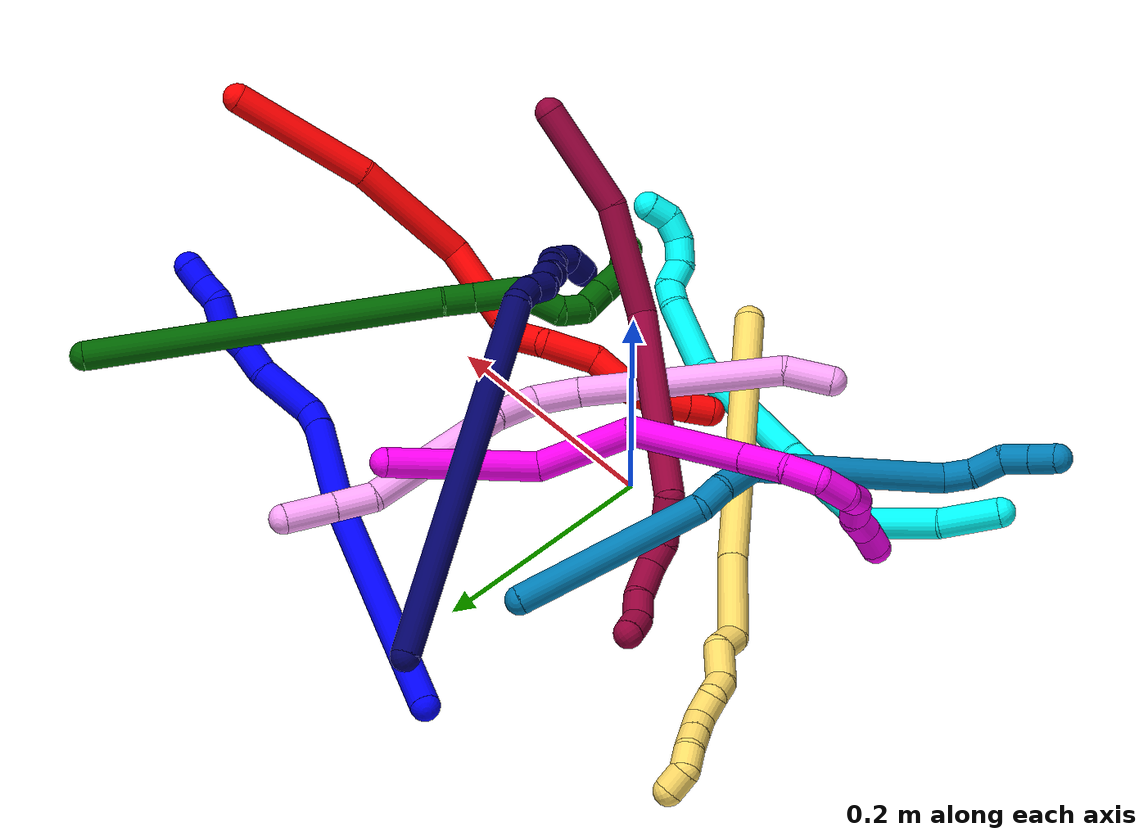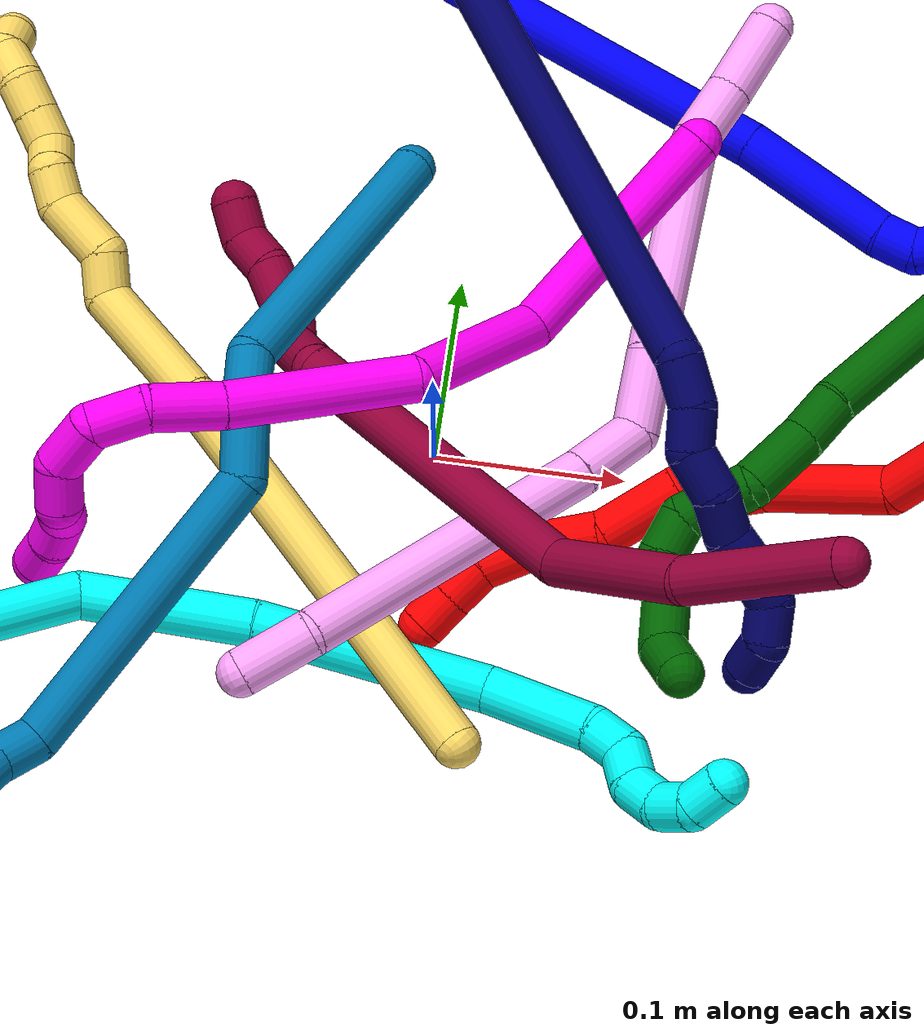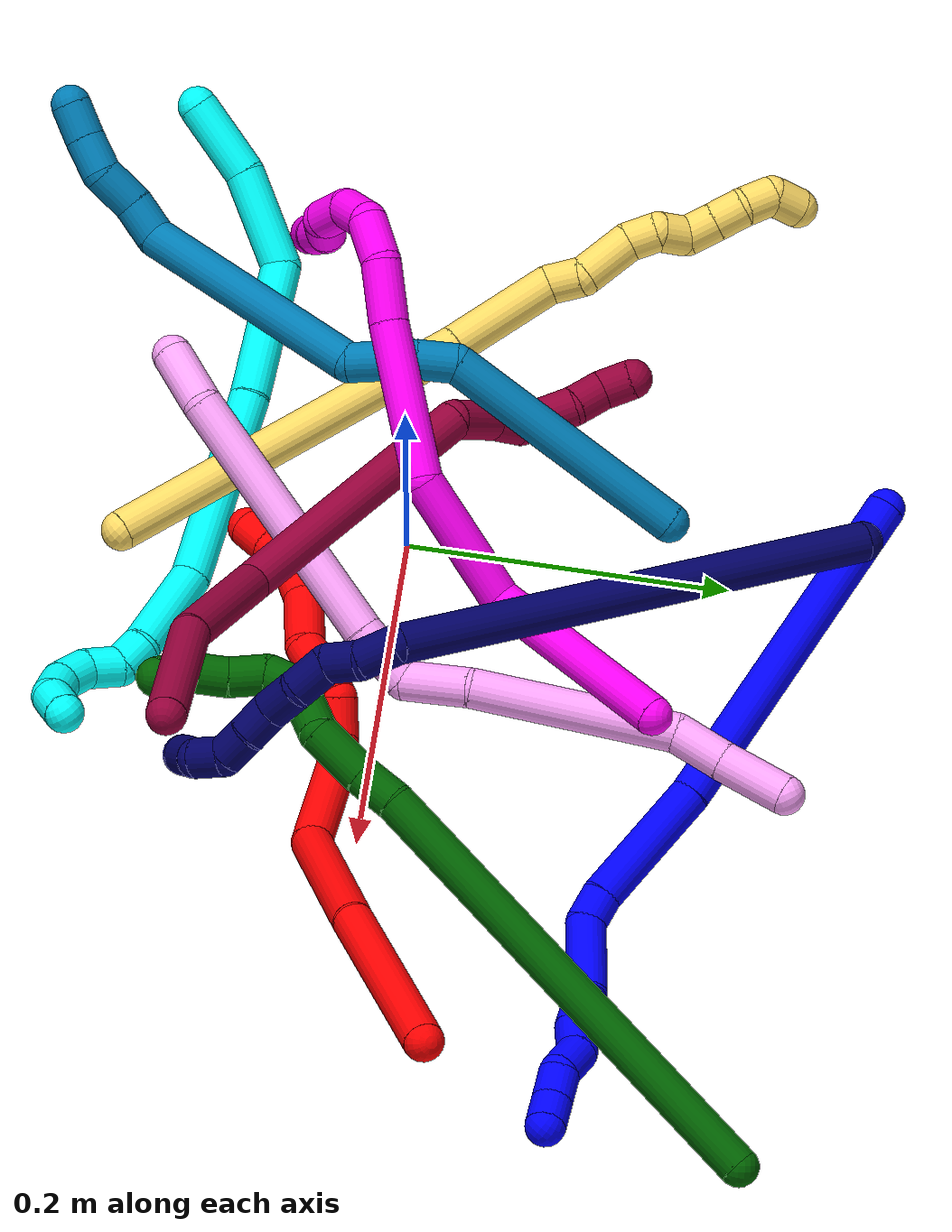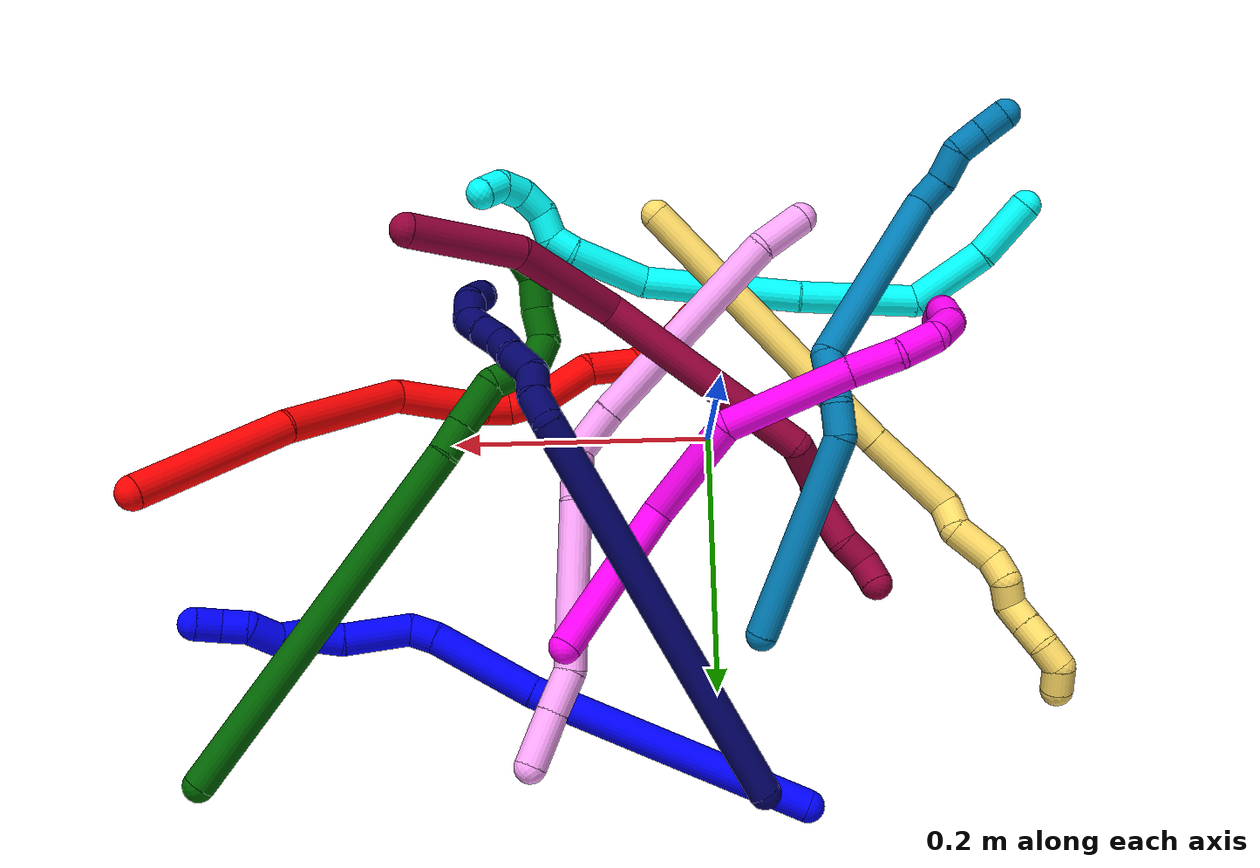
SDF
<sdf version="1.7">
 <world name="default">
  <plugin name="TubeGeneratorPlugin" filename="libtube_generator_plugin.so"/>
  <model name="photoneo_s_sensor">
   <static>1</static>
   <pose>0 0 2 1.57079 1.57079 3.14159</pose>
   <link name="link">
    <inertial><mass>0.1</mass></inertial>
    <sensor name="sensor" type="depth">
     <update_rate>30</update_rate>
     <camera>
      <horizontal_fov>1.22</horizontal_fov>
      <image><width>1920</width><height>1200</height><format>B8G8R8</format></image>
      <clip><near>0.1</near><far>4</far></clip>
      <depth_camera><output>points</output></depth_camera>
     </camera>
     <plugin name="camera_plugin" filename="libgazebo_ros_depth_camera.so">
      <baseline>0.2</baseline>
      <alwaysOn>1</alwaysOn>
      <updateRate>0.0</updateRate>
      <cameraName>camera_ir</cameraName>
      <imageTopicName>/camera/color/image_raw</imageTopicName>
      <cameraInfoTopicName>/camera/color/camera_info</cameraInfoTopicName>
      <depthImageTopicName>/camera/depth/image_raw</depthImageTopicName>
      <depthImageCameraInfoTopicName>/camera/depth/camera_info</depthImageCameraInfoTopicName>
      <pointCloudTopicName>/camera/depth/points</pointCloudTopicName>
      <frameName>fr_optical</frameName>
      <pointCloudCutoff>0.1</pointCloudCutoff>
      <pointCloudCutoffMax>2.0</pointCloudCutoffMax>
      <distortionK1>0</distortionK1>
      <distortionK2>0</distortionK2>
      <distortionK3>0</distortionK3>
      <distortionT1>0</distortionT1>
      <distortionT2>0</distortionT2>
      <CxPrime>0</CxPrime>
      <Cx>0</Cx>
      <Cy>0</Cy>
      <focalLength>0</focalLength>
      <hackBaseline>0</hackBaseline>
     </plugin>
    </sensor>
   </link>
  </model>
  <gravity>0 0 -9.8</gravity>
  <magnetic_field>6e-06 2.3e-05 -4.2e-05</magnetic_field>
  <atmosphere type="adiabatic"/>
  <physics name="default_physics" default="0" type="ode">
   <max_step_size>0.003</max_step_size>
   <real_time_factor>1</real_time_factor>
   <real_time_update_rate>1000</real_time_update_rate>
   <max_contacts>10000</max_contacts>
   <ode>
    <solver>
     <type>quick</type>
     <iters>100</iters>
     <sor>1.3</sor>
     <use_dynamic_moi_rescaling>0</use_dynamic_moi_rescaling>
    </solver>
    <constraints>
     <contact_max_correcting_vel>0</contact_max_correcting_vel>
     <contact_surface_layer>0.001</contact_surface_layer>
     <cfm>0</cfm>
     <erp>0.2</erp>
    </constraints>
   </ode>
  </physics>
  <scene><ambient>0.4 0.4 0.4 1</ambient><background>0.7 0.7 0.7 1</background><shadows>0</shadows></scene>
  <audio><device>default</device></audio>
  <spherical_coordinates>
   <surface_model>EARTH_WGS84</surface_model>
   <latitude_deg>0</latitude_deg>
   <longitude_deg>0</longitude_deg>
   <elevation>0</elevation>
   <heading_deg>0</heading_deg>
  </spherical_coordinates>
  <model name="bin">
   <static>1</static>
   <link name="bottom">
    <collision name="collision-bottom">
     <pose>0 0 -0.01 0 -0 0</pose>
     <geometry><box><size>0.8 0.6 0.02</size></box></geometry>
     <surface>
      <friction><ode><mu>100</mu><mu2>100</mu2></ode></friction>
      <contact><collide_bitmask>65535</collide_bitmask></contact>
     </surface>
    </collision>
   </link>
   <link name="west_wall">
    <collision name="collision-west_wall">
     <pose>-0.41 0 0.1 0 -0 0</pose>
     <geometry><box><size>0.02 0.6 0.2</size></box></geometry>
     <surface>
      <friction><ode><mu>100</mu><mu2>100</mu2></ode></friction>
      <contact><collide_bitmask>65535</collide_bitmask></contact>
     </surface>
    </collision>
   </link>
   <link name="east_wall">
    <collision name="collision-east_wall">
     <pose>0.41 0 0.1 0 -0 0</pose>
     <geometry><box><size>0.02 0.6 0.2</size></box></geometry>
     <surface>
      <friction><ode><mu>100</mu><mu2>100</mu2></ode></friction>
      <contact><collide_bitmask>65535</collide_bitmask></contact>
     </surface>
    </collision>
   </link>
   <link name="south_wall">
    <collision name="collision-south_wall">
     <pose>0 -0.31 0.1 0 -0 0</pose>
     <geometry><box><size>0.8 0.02 0.2</size></box></geometry>
     <surface>
      <friction><ode><mu>100</mu><mu2>100</mu2></ode></friction>
      <contact><collide_bitmask>65535</collide_bitmask></contact>
     </surface>
    </collision>
   </link>
   <link name="north_wall">
    <collision name="collision-north_wall">
     <pose>0 0.31 0.1 0 -0 0</pose>
     <geometry><box><size>0.8 0.02 0.2</size></box></geometry>
     <surface>
      <friction><ode><mu>100</mu><mu2>100</mu2></ode></friction>
      <contact><collide_bitmask>65535</collide_bitmask></contact>
     </surface>
    </collision>
   </link>
  </model>
  <model name="1">
   <static>0</static>
   <link name="1">
    <collision name="collision-cylinder-e_1_1_4">
     <pose>0.052959 -0.012417 0.09868 0.125169 0.489285 0.031286</pose>
     <geometry><cylinder><radius>0.0125</radius><length>0.225358</length></cylinder></geometry>
     <surface>
      <friction><ode><mu>1.16</mu><mu2>1.16</mu2><slip1>0</slip1><slip2>0</slip2></ode></friction>
      <contact><ode><kp>1e+06</kp><kd>1</kd><max_vel>0</max_vel><min_depth>0.001</min_depth></ode></contact>
     </surface>
    </collision>
    <visual name="visual-cylinder-e_1_1_4">
     <pose>0.052959 -0.012417 0.09868 0.125169 0.489285 0.031286</pose>
     <geometry><cylinder><radius>0.0125</radius><length>0.225358</length></cylinder></geometry>
     <material><ambient>0 0 1 1</ambient></material>
    </visual>
    <collision name="collision-cylinder-e_2_4_5">
     <pose>0.126225 -0.02467 0.234997 -0.00434 0.494817 -0.001096</pose>
     <geometry><cylinder><radius>0.0125</radius><length>0.085532</length></cylinder></geometry>
     <surface>
      <friction><ode><mu>1.16</mu><mu2>1.16</mu2><slip1>0</slip1><slip2>0</slip2></ode></friction>
      <contact><ode><kp>1e+06</kp><kd>1</kd><max_vel>0</max_vel><min_depth>0.001</min_depth></ode></contact>
     </surface>
    </collision>
    <visual name="visual-cylinder-e_2_4_5">
     <pose>0.126225 -0.02467 0.234997 -0.00434 0.494817 -0.001096</pose>
     <geometry><cylinder><radius>0.0125</radius><length>0.085532</length></cylinder></geometry>
     <material><ambient>0 0 1 1</ambient></material>
    </visual>
    <collision name="collision-cylinder-e_3_5_6">
     <pose>0.151455 -0.026395 0.281561 0.208435 0.494575 0.0528</pose>
     <geometry><cylinder><radius>0.0125</radius><length>0.020736</length></cylinder></geometry>
     <surface>
      <friction><ode><mu>1.16</mu><mu2>1.16</mu2><slip1>0</slip1><slip2>0</slip2></ode></friction>
      <contact><ode><kp>1e+06</kp><kd>1</kd><max_vel>0</max_vel><min_depth>0.001</min_depth></ode></contact>
     </surface>
    </collision>
    <visual name="visual-cylinder-e_3_5_6">
     <pose>0.151455 -0.026395 0.281561 0.208435 0.494575 0.0528</pose>
     <geometry><cylinder><radius>0.0125</radius><length>0.020736</length></cylinder></geometry>
     <material><ambient>0 0 1 1</ambient></material>
    </visual>
    <collision name="collision-cylinder-e_4_6_7">
     <pose>0.173511 -0.043278 0.30361 0.851908 0.710239 0.333403</pose>
     <geometry><cylinder><radius>0.0125</radius><length>0.052559</length></cylinder></geometry>
     <surface>
      <friction><ode><mu>1.16</mu><mu2>1.16</mu2><slip1>0</slip1><slip2>0</slip2></ode></friction>
      <contact><ode><kp>1e+06</kp><kd>1</kd><max_vel>0</max_vel><min_depth>0.001</min_depth></ode></contact>
     </surface>
    </collision>
    <visual name="visual-cylinder-e_4_6_7">
     <pose>0.173511 -0.043278 0.30361 0.851908 0.710239 0.333403</pose>
     <geometry><cylinder><radius>0.0125</radius><length>0.052559</length></cylinder></geometry>
     <material><ambient>0 0 1 1</ambient></material>
    </visual>
    <collision name="collision-cylinder-e_5_7_8">
     <pose>0.19982 -0.062773 0.325468 0.475736 0.751078 0.190599</pose>
     <geometry><cylinder><radius>0.0125</radius><length>0.026888</length></cylinder></geometry>
     <surface>
      <friction><ode><mu>1.16</mu><mu2>1.16</mu2><slip1>0</slip1><slip2>0</slip2></ode></friction>
      <contact><ode><kp>1e+06</kp><kd>1</kd><max_vel>0</max_vel><min_depth>0.001</min_depth></ode></contact>
     </surface>
    </collision>
    <visual name="visual-cylinder-e_5_7_8">
     <pose>0.19982 -0.062773 0.325468 0.475736 0.751078 0.190599</pose>
     <geometry><cylinder><radius>0.0125</radius><length>0.026888</length></cylinder></geometry>
     <material><ambient>0 0 1 1</ambient></material>
    </visual>
    <collision name="collision-cylinder-e_6_8_9">
     <pose>0.218655 -0.073269 0.337619 1.05292 0.950582 0.581249</pose>
     <geometry><cylinder><radius>0.0125</radius><length>0.023744</length></cylinder></geometry>
     <surface>
      <friction><ode><mu>1.16</mu><mu2>1.16</mu2><slip1>0</slip1><slip2>0</slip2></ode></friction>
      <contact><ode><kp>1e+06</kp><kd>1</kd><max_vel>0</max_vel><min_depth>0.001</min_depth></ode></contact>
     </surface>
    </collision>
    <visual name="visual-cylinder-e_6_8_9">
     <pose>0.218655 -0.073269 0.337619 1.05292 0.950582 0.581249</pose>
     <geometry><cylinder><radius>0.0125</radius><length>0.023744</length></cylinder></geometry>
     <material><ambient>0 0 1 1</ambient></material>
    </visual>
    <collision name="collision-cylinder-e_7_9_10">
     <pose>0.239248 -0.079718 0.347064 0.075242 1.06565 0.044386</pose>
     <geometry><cylinder><radius>0.0125</radius><length>0.024986</length></cylinder></geometry>
     <surface>
      <friction><ode><mu>1.16</mu><mu2>1.16</mu2><slip1>0</slip1><slip2>0</slip2></ode></friction>
      <contact><ode><kp>1e+06</kp><kd>1</kd><max_vel>0</max_vel><min_depth>0.001</min_depth></ode></contact>
     </surface>
    </collision>
    <visual name="visual-cylinder-e_7_9_10">
     <pose>0.239248 -0.079718 0.347064 0.075242 1.06565 0.044386</pose>
     <geometry><cylinder><radius>0.0125</radius><length>0.024986</length></cylinder></geometry>
     <material><ambient>0 0 1 1</ambient></material>
    </visual>
    <collision name="collision-cylinder-e_8_10_11">
     <pose>0.256061 -0.084327 0.360164 0.53118 0.622002 0.174425</pose>
     <geometry><cylinder><radius>0.0125</radius><length>0.020183</length></cylinder></geometry>
     <surface>
      <friction><ode><mu>1.16</mu><mu2>1.16</mu2><slip1>0</slip1><slip2>0</slip2></ode></friction>
      <contact><ode><kp>1e+06</kp><kd>1</kd><max_vel>0</max_vel><min_depth>0.001</min_depth></ode></contact>
     </surface>
    </collision>
    <visual name="visual-cylinder-e_8_10_11">
     <pose>0.256061 -0.084327 0.360164 0.53118 0.622002 0.174425</pose>
     <geometry><cylinder><radius>0.0125</radius><length>0.020183</length></cylinder></geometry>
     <material><ambient>0 0 1 1</ambient></material>
    </visual>
    <collision name="collision-cylinder-e_9_11_2">
     <pose>0.269401 -0.092162 0.372799 0.584389 0.841222 0.267496</pose>
     <geometry><cylinder><radius>0.0125</radius><length>0.020015</length></cylinder></geometry>
     <surface>
      <friction><ode><mu>1.16</mu><mu2>1.16</mu2><slip1>0</slip1><slip2>0</slip2></ode></friction>
      <contact><ode><kp>1e+06</kp><kd>1</kd><max_vel>0</max_vel><min_depth>0.001</min_depth></ode></contact>
     </surface>
    </collision>
    <visual name="visual-cylinder-e_9_11_2">
     <pose>0.269401 -0.092162 0.372799 0.584389 0.841222 0.267496</pose>
     <geometry><cylinder><radius>0.0125</radius><length>0.020015</length></cylinder></geometry>
     <material><ambient>0 0 1 1</ambient></material>
    </visual>
    <collision name="collision-sphere-2">
     <pose>0.276861 -0.095842 0.378362 0 -0 0</pose>
     <geometry><sphere><radius>0.0125</radius></sphere></geometry>
     <surface>
      <friction><ode><mu>1.16</mu><mu2>1.16</mu2><slip1>0</slip1><slip2>0</slip2></ode></friction>
      <contact><ode><kp>1e+06</kp><kd>1</kd><max_vel>0</max_vel><min_depth>0.001</min_depth></ode></contact>
     </surface>
    </collision>
    <visual name="visual-sphere-2">
     <pose>0.276861 -0.095842 0.378362 0 -0 0</pose>
     <geometry><sphere><radius>0.0125</radius></sphere></geometry>
     <material><ambient>0 0 1 1</ambient></material>
    </visual>
    <collision name="collision-sphere-11">
     <pose>0.261941 -0.088482 0.367235 0 -0 0</pose>
     <geometry><sphere><radius>0.0125</radius></sphere></geometry>
     <surface>
      <friction><ode><mu>1.16</mu><mu2>1.16</mu2><slip1>0</slip1><slip2>0</slip2></ode></friction>
      <contact><ode><kp>1e+06</kp><kd>1</kd><max_vel>0</max_vel><min_depth>0.001</min_depth></ode></contact>
     </surface>
    </collision>
    <visual name="visual-sphere-11">
     <pose>0.261941 -0.088482 0.367235 0 -0 0</pose>
     <geometry><sphere><radius>0.0125</radius></sphere></geometry>
     <material><ambient>0 0 1 1</ambient></material>
    </visual>
    <collision name="collision-sphere-10">
     <pose>0.250181 -0.080173 0.353092 0 -0 0</pose>
     <geometry><sphere><radius>0.0125</radius></sphere></geometry>
     <surface>
      <friction><ode><mu>1.16</mu><mu2>1.16</mu2><slip1>0</slip1><slip2>0</slip2></ode></friction>
      <contact><ode><kp>1e+06</kp><kd>1</kd><max_vel>0</max_vel><min_depth>0.001</min_depth></ode></contact>
     </surface>
    </collision>
    <visual name="visual-sphere-10">
     <pose>0.250181 -0.080173 0.353092 0 -0 0</pose>
     <geometry><sphere><radius>0.0125</radius></sphere></geometry>
     <material><ambient>0 0 1 1</ambient></material>
    </visual>
    <collision name="collision-sphere-9">
     <pose>0.228316 -0.079264 0.341035 0 -0 0</pose>
     <geometry><sphere><radius>0.0125</radius></sphere></geometry>
     <surface>
      <friction><ode><mu>1.16</mu><mu2>1.16</mu2><slip1>0</slip1><slip2>0</slip2></ode></friction>
      <contact><ode><kp>1e+06</kp><kd>1</kd><max_vel>0</max_vel><min_depth>0.001</min_depth></ode></contact>
     </surface>
    </collision>
    <visual name="visual-sphere-9">
     <pose>0.228316 -0.079264 0.341035 0 -0 0</pose>
     <geometry><sphere><radius>0.0125</radius></sphere></geometry>
     <material><ambient>0 0 1 1</ambient></material>
    </visual>
    <collision name="collision-sphere-4">
     <pose>0.105917 -0.024833 0.197361 0 -0 0</pose>
     <geometry><sphere><radius>0.0125</radius></sphere></geometry>
     <surface>
      <friction><ode><mu>1.16</mu><mu2>1.16</mu2><slip1>0</slip1><slip2>0</slip2></ode></friction>
      <contact><ode><kp>1e+06</kp><kd>1</kd><max_vel>0</max_vel><min_depth>0.001</min_depth></ode></contact>
     </surface>
    </collision>
    <visual name="visual-sphere-4">
     <pose>0.105917 -0.024833 0.197361 0 -0 0</pose>
     <geometry><sphere><radius>0.0125</radius></sphere></geometry>
     <material><ambient>0 0 1 1</ambient></material>
    </visual>
    <collision name="collision-sphere-1">
     <geometry><sphere><radius>0.0125</radius></sphere></geometry>
     <surface>
      <friction><ode><mu>1.16</mu><mu2>1.16</mu2><slip1>0</slip1><slip2>0</slip2></ode></friction>
      <contact><ode><kp>1e+06</kp><kd>1</kd><max_vel>0</max_vel><min_depth>0.001</min_depth></ode></contact>
     </surface>
    </collision>
    <visual name="visual-sphere-1">
     <geometry><sphere><radius>0.0125</radius></sphere></geometry>
     <material><ambient>0 0 1 1</ambient></material>
    </visual>
    <collision name="collision-sphere-8">
     <pose>0.208994 -0.067274 0.334203 0 -0 0</pose>
     <geometry><sphere><radius>0.0125</radius></sphere></geometry>
     <surface>
      <friction><ode><mu>1.16</mu><mu2>1.16</mu2><slip1>0</slip1><slip2>0</slip2></ode></friction>
      <contact><ode><kp>1e+06</kp><kd>1</kd><max_vel>0</max_vel><min_depth>0.001</min_depth></ode></contact>
     </surface>
    </collision>
    <visual name="visual-sphere-8">
     <pose>0.208994 -0.067274 0.334203 0 -0 0</pose>
     <geometry><sphere><radius>0.0125</radius></sphere></geometry>
     <material><ambient>0 0 1 1</ambient></material>
    </visual>
    <collision name="collision-sphere-5">
     <pose>0.146534 -0.024507 0.272633 0 -0 0</pose>
     <geometry><sphere><radius>0.0125</radius></sphere></geometry>
     <surface>
      <friction><ode><mu>1.16</mu><mu2>1.16</mu2><slip1>0</slip1><slip2>0</slip2></ode></friction>
      <contact><ode><kp>1e+06</kp><kd>1</kd><max_vel>0</max_vel><min_depth>0.001</min_depth></ode></contact>
     </surface>
    </collision>
    <visual name="visual-sphere-5">
     <pose>0.146534 -0.024507 0.272633 0 -0 0</pose>
     <geometry><sphere><radius>0.0125</radius></sphere></geometry>
     <material><ambient>0 0 1 1</ambient></material>
    </visual>
    <collision name="collision-sphere-6">
     <pose>0.156376 -0.028283 0.290489 0 -0 0</pose>
     <geometry><sphere><radius>0.0125</radius></sphere></geometry>
     <surface>
      <friction><ode><mu>1.16</mu><mu2>1.16</mu2><slip1>0</slip1><slip2>0</slip2></ode></friction>
      <contact><ode><kp>1e+06</kp><kd>1</kd><max_vel>0</max_vel><min_depth>0.001</min_depth></ode></contact>
     </surface>
    </collision>
    <visual name="visual-sphere-6">
     <pose>0.156376 -0.028283 0.290489 0 -0 0</pose>
     <geometry><sphere><radius>0.0125</radius></sphere></geometry>
     <material><ambient>0 0 1 1</ambient></material>
    </visual>
    <collision name="collision-sphere-7">
     <pose>0.190645 -0.058272 0.316732 0 -0 0</pose>
     <geometry><sphere><radius>0.0125</radius></sphere></geometry>
     <surface>
      <friction><ode><mu>1.16</mu><mu2>1.16</mu2><slip1>0</slip1><slip2>0</slip2></ode></friction>
      <contact><ode><kp>1e+06</kp><kd>1</kd><max_vel>0</max_vel><min_depth>0.001</min_depth></ode></contact>
     </surface>
    </collision>
    <visual name="visual-sphere-7">
     <pose>0.190645 -0.058272 0.316732 0 -0 0</pose>
     <geometry><sphere><radius>0.0125</radius></sphere></geometry>
     <material><ambient>0 0 1 1</ambient></material>
    </visual>
    <inertial>
     <pose>0.124187 -0.033392 0.208607 0 -0 0</pose>
     <mass>0.5</mass>
     <inertia>
      <ixx>0.000969</ixx>
      <ixy>0</ixy>
      <ixz>0</ixz>
      <iyy>0.001058</iyy>
      <iyz>0</iyz>
      <izz>-0.000349</izz>
     </inertia>
    </inertial>
   </link>
   <pose>-0.064449 0.287908 0.011711 2.85591 -1.07517 -0.275014</pose>
  </model>
  <model name="2">
   <static>0</static>
   <link name="2">
    <collision name="collision-cylinder-e_1_1_4">
     <pose>-0.027574 -0.014832 -0.052917 2.86832 -0.465045 -2.0895</pose>
     <geometry><cylinder><radius>0.0125</radius><length>0.122972</length></cylinder></geometry>
     <surface>
      <friction><ode><mu>1.16</mu><mu2>1.16</mu2><slip1>0</slip1><slip2>0</slip2></ode></friction>
      <contact><ode><kp>1e+06</kp><kd>1</kd><max_vel>0</max_vel><min_depth>0.001</min_depth></ode></contact>
     </surface>
    </collision>
    <visual name="visual-cylinder-e_1_1_4">
     <pose>-0.027574 -0.014832 -0.052917 2.86832 -0.465045 -2.0895</pose>
     <geometry><cylinder><radius>0.0125</radius><length>0.122972</length></cylinder></geometry>
     <material><ambient>1 0 0 1</ambient></material>
    </visual>
    <collision name="collision-cylinder-e_2_4_5">
     <pose>-0.076018 -0.033018 -0.153316 3.07107 -0.413194 -2.80812</pose>
     <geometry><cylinder><radius>0.0125</radius><length>0.10395</length></cylinder></geometry>
     <surface>
      <friction><ode><mu>1.16</mu><mu2>1.16</mu2><slip1>0</slip1><slip2>0</slip2></ode></friction>
      <contact><ode><kp>1e+06</kp><kd>1</kd><max_vel>0</max_vel><min_depth>0.001</min_depth></ode></contact>
     </surface>
    </collision>
    <visual name="visual-cylinder-e_2_4_5">
     <pose>-0.076018 -0.033018 -0.153316 3.07107 -0.413194 -2.80812</pose>
     <geometry><cylinder><radius>0.0125</radius><length>0.10395</length></cylinder></geometry>
     <material><ambient>1 0 0 1</ambient></material>
    </visual>
    <collision name="collision-cylinder-e_3_5_6">
     <pose>-0.124216 -0.03178 -0.22215 -2.92974 -0.896573 2.70645</pose>
     <geometry><cylinder><radius>0.0125</radius><length>0.069964</length></cylinder></geometry>
     <surface>
      <friction><ode><mu>1.16</mu><mu2>1.16</mu2><slip1>0</slip1><slip2>0</slip2></ode></friction>
      <contact><ode><kp>1e+06</kp><kd>1</kd><max_vel>0</max_vel><min_depth>0.001</min_depth></ode></contact>
     </surface>
    </collision>
    <visual name="visual-cylinder-e_3_5_6">
     <pose>-0.124216 -0.03178 -0.22215 -2.92974 -0.896573 2.70645</pose>
     <geometry><cylinder><radius>0.0125</radius><length>0.069964</length></cylinder></geometry>
     <material><ambient>1 0 0 1</ambient></material>
    </visual>
    <collision name="collision-cylinder-e_4_6_7">
     <pose>-0.15955 -0.02721 -0.251142 3.13864 -0.808717 -3.13469</pose>
     <geometry><cylinder><radius>0.0125</radius><length>0.022136</length></cylinder></geometry>
     <surface>
      <friction><ode><mu>1.16</mu><mu2>1.16</mu2><slip1>0</slip1><slip2>0</slip2></ode></friction>
      <contact><ode><kp>1e+06</kp><kd>1</kd><max_vel>0</max_vel><min_depth>0.001</min_depth></ode></contact>
     </surface>
    </collision>
    <visual name="visual-cylinder-e_4_6_7">
     <pose>-0.15955 -0.02721 -0.251142 3.13864 -0.808717 -3.13469</pose>
     <geometry><cylinder><radius>0.0125</radius><length>0.022136</length></cylinder></geometry>
     <material><ambient>1 0 0 1</ambient></material>
    </visual>
    <collision name="collision-cylinder-e_5_7_8">
     <pose>-0.17903 -0.033687 -0.260366 1.81124 -1.04582 -1.26746</pose>
     <geometry><cylinder><radius>0.0125</radius><length>0.026519</length></cylinder></geometry>
     <surface>
      <friction><ode><mu>1.16</mu><mu2>1.16</mu2><slip1>0</slip1><slip2>0</slip2></ode></friction>
      <contact><ode><kp>1e+06</kp><kd>1</kd><max_vel>0</max_vel><min_depth>0.001</min_depth></ode></contact>
     </surface>
    </collision>
    <visual name="visual-cylinder-e_5_7_8">
     <pose>-0.17903 -0.033687 -0.260366 1.81124 -1.04582 -1.26746</pose>
     <geometry><cylinder><radius>0.0125</radius><length>0.026519</length></cylinder></geometry>
     <material><ambient>1 0 0 1</ambient></material>
    </visual>
    <collision name="collision-cylinder-e_6_8_9">
     <pose>-0.201649 -0.050574 -0.2782 2.5709 -0.52342 -1.47999</pose>
     <geometry><cylinder><radius>0.0125</radius><length>0.044593</length></cylinder></geometry>
     <surface>
      <friction><ode><mu>1.16</mu><mu2>1.16</mu2><slip1>0</slip1><slip2>0</slip2></ode></friction>
      <contact><ode><kp>1e+06</kp><kd>1</kd><max_vel>0</max_vel><min_depth>0.001</min_depth></ode></contact>
     </surface>
    </collision>
    <visual name="visual-cylinder-e_6_8_9">
     <pose>-0.201649 -0.050574 -0.2782 2.5709 -0.52342 -1.47999</pose>
     <geometry><cylinder><radius>0.0125</radius><length>0.044593</length></cylinder></geometry>
     <material><ambient>1 0 0 1</ambient></material>
    </visual>
    <collision name="collision-cylinder-e_7_9_10">
     <pose>-0.227696 -0.063335 -0.308081 2.97234 -0.822768 -2.7575</pose>
     <geometry><cylinder><radius>0.0125</radius><length>0.040659</length></cylinder></geometry>
     <surface>
      <friction><ode><mu>1.16</mu><mu2>1.16</mu2><slip1>0</slip1><slip2>0</slip2></ode></friction>
      <contact><ode><kp>1e+06</kp><kd>1</kd><max_vel>0</max_vel><min_depth>0.001</min_depth></ode></contact>
     </surface>
    </collision>
    <visual name="visual-cylinder-e_7_9_10">
     <pose>-0.227696 -0.063335 -0.308081 2.97234 -0.822768 -2.7575</pose>
     <geometry><cylinder><radius>0.0125</radius><length>0.040659</length></cylinder></geometry>
     <material><ambient>1 0 0 1</ambient></material>
    </visual>
    <collision name="collision-cylinder-e_8_10_11">
     <pose>-0.250984 -0.071261 -0.330193 2.55835 -0.689914 -1.74968</pose>
     <geometry><cylinder><radius>0.0125</radius><length>0.026351</length></cylinder></geometry>
     <surface>
      <friction><ode><mu>1.16</mu><mu2>1.16</mu2><slip1>0</slip1><slip2>0</slip2></ode></friction>
      <contact><ode><kp>1e+06</kp><kd>1</kd><max_vel>0</max_vel><min_depth>0.001</min_depth></ode></contact>
     </surface>
    </collision>
    <visual name="visual-cylinder-e_8_10_11">
     <pose>-0.250984 -0.071261 -0.330193 2.55835 -0.689914 -1.74968</pose>
     <geometry><cylinder><radius>0.0125</radius><length>0.026351</length></cylinder></geometry>
     <material><ambient>1 0 0 1</ambient></material>
    </visual>
    <collision name="collision-cylinder-e_9_11_12">
     <pose>-0.262471 -0.082412 -0.347653 2.58753 -0.285797 -0.93688</pose>
     <geometry><cylinder><radius>0.0125</radius><length>0.022006</length></cylinder></geometry>
     <surface>
      <friction><ode><mu>1.16</mu><mu2>1.16</mu2><slip1>0</slip1><slip2>0</slip2></ode></friction>
      <contact><ode><kp>1e+06</kp><kd>1</kd><max_vel>0</max_vel><min_depth>0.001</min_depth></ode></contact>
     </surface>
    </collision>
    <visual name="visual-cylinder-e_9_11_12">
     <pose>-0.262471 -0.082412 -0.347653 2.58753 -0.285797 -0.93688</pose>
     <geometry><cylinder><radius>0.0125</radius><length>0.022006</length></cylinder></geometry>
     <material><ambient>1 0 0 1</ambient></material>
    </visual>
    <collision name="collision-cylinder-e_10_12_2">
     <pose>-0.268248 -0.093642 -0.364956 2.54327 -0.259473 -0.8004</pose>
     <geometry><cylinder><radius>0.0125</radius><length>0.020852</length></cylinder></geometry>
     <surface>
      <friction><ode><mu>1.16</mu><mu2>1.16</mu2><slip1>0</slip1><slip2>0</slip2></ode></friction>
      <contact><ode><kp>1e+06</kp><kd>1</kd><max_vel>0</max_vel><min_depth>0.001</min_depth></ode></contact>
     </surface>
    </collision>
    <visual name="visual-cylinder-e_10_12_2">
     <pose>-0.268248 -0.093642 -0.364956 2.54327 -0.259473 -0.8004</pose>
     <geometry><cylinder><radius>0.0125</radius><length>0.020852</length></cylinder></geometry>
     <material><ambient>1 0 0 1</ambient></material>
    </visual>
    <collision name="collision-sphere-2">
     <pose>-0.270923 -0.099318 -0.373282 0 -0 0</pose>
     <geometry><sphere><radius>0.0125</radius></sphere></geometry>
     <surface>
      <friction><ode><mu>1.16</mu><mu2>1.16</mu2><slip1>0</slip1><slip2>0</slip2></ode></friction>
      <contact><ode><kp>1e+06</kp><kd>1</kd><max_vel>0</max_vel><min_depth>0.001</min_depth></ode></contact>
     </surface>
    </collision>
    <visual name="visual-sphere-2">
     <pose>-0.270923 -0.099318 -0.373282 0 -0 0</pose>
     <geometry><sphere><radius>0.0125</radius></sphere></geometry>
     <material><ambient>1 0 0 1</ambient></material>
    </visual>
    <collision name="collision-sphere-12">
     <pose>-0.265573 -0.087966 -0.35663 0 -0 0</pose>
     <geometry><sphere><radius>0.0125</radius></sphere></geometry>
     <surface>
      <friction><ode><mu>1.16</mu><mu2>1.16</mu2><slip1>0</slip1><slip2>0</slip2></ode></friction>
      <contact><ode><kp>1e+06</kp><kd>1</kd><max_vel>0</max_vel><min_depth>0.001</min_depth></ode></contact>
     </surface>
    </collision>
    <visual name="visual-sphere-12">
     <pose>-0.265573 -0.087966 -0.35663 0 -0 0</pose>
     <geometry><sphere><radius>0.0125</radius></sphere></geometry>
     <material><ambient>1 0 0 1</ambient></material>
    </visual>
    <collision name="collision-sphere-11">
     <pose>-0.259369 -0.076858 -0.338675 0 -0 0</pose>
     <geometry><sphere><radius>0.0125</radius></sphere></geometry>
     <surface>
      <friction><ode><mu>1.16</mu><mu2>1.16</mu2><slip1>0</slip1><slip2>0</slip2></ode></friction>
      <contact><ode><kp>1e+06</kp><kd>1</kd><max_vel>0</max_vel><min_depth>0.001</min_depth></ode></contact>
     </surface>
    </collision>
    <visual name="visual-sphere-11">
     <pose>-0.259369 -0.076858 -0.338675 0 -0 0</pose>
     <geometry><sphere><radius>0.0125</radius></sphere></geometry>
     <material><ambient>1 0 0 1</ambient></material>
    </visual>
    <collision name="collision-sphere-10">
     <pose>-0.242598 -0.065665 -0.321711 0 -0 0</pose>
     <geometry><sphere><radius>0.0125</radius></sphere></geometry>
     <surface>
      <friction><ode><mu>1.16</mu><mu2>1.16</mu2><slip1>0</slip1><slip2>0</slip2></ode></friction>
      <contact><ode><kp>1e+06</kp><kd>1</kd><max_vel>0</max_vel><min_depth>0.001</min_depth></ode></contact>
     </surface>
    </collision>
    <visual name="visual-sphere-10">
     <pose>-0.242598 -0.065665 -0.321711 0 -0 0</pose>
     <geometry><sphere><radius>0.0125</radius></sphere></geometry>
     <material><ambient>1 0 0 1</ambient></material>
    </visual>
    <collision name="collision-sphere-9">
     <pose>-0.212794 -0.061006 -0.294451 0 -0 0</pose>
     <geometry><sphere><radius>0.0125</radius></sphere></geometry>
     <surface>
      <friction><ode><mu>1.16</mu><mu2>1.16</mu2><slip1>0</slip1><slip2>0</slip2></ode></friction>
      <contact><ode><kp>1e+06</kp><kd>1</kd><max_vel>0</max_vel><min_depth>0.001</min_depth></ode></contact>
     </surface>
    </collision>
    <visual name="visual-sphere-9">
     <pose>-0.212794 -0.061006 -0.294451 0 -0 0</pose>
     <geometry><sphere><radius>0.0125</radius></sphere></geometry>
     <material><ambient>1 0 0 1</ambient></material>
    </visual>
    <collision name="collision-sphere-4">
     <pose>-0.055148 -0.029664 -0.105834 0 -0 0</pose>
     <geometry><sphere><radius>0.0125</radius></sphere></geometry>
     <surface>
      <friction><ode><mu>1.16</mu><mu2>1.16</mu2><slip1>0</slip1><slip2>0</slip2></ode></friction>
      <contact><ode><kp>1e+06</kp><kd>1</kd><max_vel>0</max_vel><min_depth>0.001</min_depth></ode></contact>
     </surface>
    </collision>
    <visual name="visual-sphere-4">
     <pose>-0.055148 -0.029664 -0.105834 0 -0 0</pose>
     <geometry><sphere><radius>0.0125</radius></sphere></geometry>
     <material><ambient>1 0 0 1</ambient></material>
    </visual>
    <collision name="collision-sphere-1">
     <geometry><sphere><radius>0.0125</radius></sphere></geometry>
     <surface>
      <friction><ode><mu>1.16</mu><mu2>1.16</mu2><slip1>0</slip1><slip2>0</slip2></ode></friction>
      <contact><ode><kp>1e+06</kp><kd>1</kd><max_vel>0</max_vel><min_depth>0.001</min_depth></ode></contact>
     </surface>
    </collision>
    <visual name="visual-sphere-1">
     <geometry><sphere><radius>0.0125</radius></sphere></geometry>
     <material><ambient>1 0 0 1</ambient></material>
    </visual>
    <collision name="collision-sphere-8">
     <pose>-0.190504 -0.040141 -0.261949 0 -0 0</pose>
     <geometry><sphere><radius>0.0125</radius></sphere></geometry>
     <surface>
      <friction><ode><mu>1.16</mu><mu2>1.16</mu2><slip1>0</slip1><slip2>0</slip2></ode></friction>
      <contact><ode><kp>1e+06</kp><kd>1</kd><max_vel>0</max_vel><min_depth>0.001</min_depth></ode></contact>
     </surface>
    </collision>
    <visual name="visual-sphere-8">
     <pose>-0.190504 -0.040141 -0.261949 0 -0 0</pose>
     <geometry><sphere><radius>0.0125</radius></sphere></geometry>
     <material><ambient>1 0 0 1</ambient></material>
    </visual>
    <collision name="collision-sphere-5">
     <pose>-0.096888 -0.036372 -0.200799 0 -0 0</pose>
     <geometry><sphere><radius>0.0125</radius></sphere></geometry>
     <surface>
      <friction><ode><mu>1.16</mu><mu2>1.16</mu2><slip1>0</slip1><slip2>0</slip2></ode></friction>
      <contact><ode><kp>1e+06</kp><kd>1</kd><max_vel>0</max_vel><min_depth>0.001</min_depth></ode></contact>
     </surface>
    </collision>
    <visual name="visual-sphere-5">
     <pose>-0.096888 -0.036372 -0.200799 0 -0 0</pose>
     <geometry><sphere><radius>0.0125</radius></sphere></geometry>
     <material><ambient>1 0 0 1</ambient></material>
    </visual>
    <collision name="collision-sphere-6">
     <pose>-0.151543 -0.027188 -0.2435 0 -0 0</pose>
     <geometry><sphere><radius>0.0125</radius></sphere></geometry>
     <surface>
      <friction><ode><mu>1.16</mu><mu2>1.16</mu2><slip1>0</slip1><slip2>0</slip2></ode></friction>
      <contact><ode><kp>1e+06</kp><kd>1</kd><max_vel>0</max_vel><min_depth>0.001</min_depth></ode></contact>
     </surface>
    </collision>
    <visual name="visual-sphere-6">
     <pose>-0.151543 -0.027188 -0.2435 0 -0 0</pose>
     <geometry><sphere><radius>0.0125</radius></sphere></geometry>
     <material><ambient>1 0 0 1</ambient></material>
    </visual>
    <collision name="collision-sphere-7">
     <pose>-0.167556 -0.027233 -0.258784 0 -0 0</pose>
     <geometry><sphere><radius>0.0125</radius></sphere></geometry>
     <surface>
      <friction><ode><mu>1.16</mu><mu2>1.16</mu2><slip1>0</slip1><slip2>0</slip2></ode></friction>
      <contact><ode><kp>1e+06</kp><kd>1</kd><max_vel>0</max_vel><min_depth>0.001</min_depth></ode></contact>
     </surface>
    </collision>
    <visual name="visual-sphere-7">
     <pose>-0.167556 -0.027233 -0.258784 0 -0 0</pose>
     <geometry><sphere><radius>0.0125</radius></sphere></geometry>
     <material><ambient>1 0 0 1</ambient></material>
    </visual>
    <inertial>
     <pose>-0.128992 -0.038899 -0.198688 0 -0 0</pose>
     <mass>0.5</mass>
     <inertia><ixx>-0.000358</ixx><ixy>0</ixy><ixz>0</ixz><iyy>6e-05</iyy><iyz>0</iyz><izz>0.000172</izz></inertia>
    </inertial>
   </link>
   <pose>0.398593 0.073394 0.212861 -0.586814 0.18581 -0.331564</pose>
  </model>
  <model name="3">
   <static>0</static>
   <link name="3">
    <collision name="collision-cylinder-e_1_1_4">
     <pose>0.004738 0.006474 -0.023976 -2.87787 0.188524 -1.23854</pose>
     <geometry><cylinder><radius>0.0125</radius><length>0.050564</length></cylinder></geometry>
     <surface>
      <friction><ode><mu>1.16</mu><mu2>1.16</mu2><slip1>0</slip1><slip2>0</slip2></ode></friction>
      <contact><ode><kp>1e+06</kp><kd>1</kd><max_vel>0</max_vel><min_depth>0.001</min_depth></ode></contact>
     </surface>
    </collision>
    <visual name="visual-cylinder-e_1_1_4">
     <pose>0.004738 0.006474 -0.023976 -2.87787 0.188524 -1.23854</pose>
     <geometry><cylinder><radius>0.0125</radius><length>0.050564</length></cylinder></geometry>
     <material><ambient>0.003922 1 0.996078 1</ambient></material>
    </visual>
    <collision name="collision-cylinder-e_2_4_5">
     <pose>0.02131 0.016194 -0.077117 -3.03073 0.383308 -2.58455</pose>
     <geometry><cylinder><radius>0.0125</radius><length>0.063284</length></cylinder></geometry>
     <surface>
      <friction><ode><mu>1.16</mu><mu2>1.16</mu2><slip1>0</slip1><slip2>0</slip2></ode></friction>
      <contact><ode><kp>1e+06</kp><kd>1</kd><max_vel>0</max_vel><min_depth>0.001</min_depth></ode></contact>
     </surface>
    </collision>
    <visual name="visual-cylinder-e_2_4_5">
     <pose>0.02131 0.016194 -0.077117 -3.03073 0.383308 -2.58455</pose>
     <geometry><cylinder><radius>0.0125</radius><length>0.063284</length></cylinder></geometry>
     <material><ambient>0.003922 1 0.996078 1</ambient></material>
    </visual>
    <collision name="collision-cylinder-e_3_5_6">
     <pose>0.07338 0.016556 -0.129421 3.01757 1.04557 2.92693</pose>
     <geometry><cylinder><radius>0.0125</radius><length>0.093009</length></cylinder></geometry>
     <surface>
      <friction><ode><mu>1.16</mu><mu2>1.16</mu2><slip1>0</slip1><slip2>0</slip2></ode></friction>
      <contact><ode><kp>1e+06</kp><kd>1</kd><max_vel>0</max_vel><min_depth>0.001</min_depth></ode></contact>
     </surface>
    </collision>
    <visual name="visual-cylinder-e_3_5_6">
     <pose>0.07338 0.016556 -0.129421 3.01757 1.04557 2.92693</pose>
     <geometry><cylinder><radius>0.0125</radius><length>0.093009</length></cylinder></geometry>
     <material><ambient>0.003922 1 0.996078 1</ambient></material>
    </visual>
    <collision name="collision-cylinder-e_4_6_7">
     <pose>0.166427 0.00204 -0.183348 2.78037 1.01349 2.50598</pose>
     <geometry><cylinder><radius>0.0125</radius><length>0.124453</length></cylinder></geometry>
     <surface>
      <friction><ode><mu>1.16</mu><mu2>1.16</mu2><slip1>0</slip1><slip2>0</slip2></ode></friction>
      <contact><ode><kp>1e+06</kp><kd>1</kd><max_vel>0</max_vel><min_depth>0.001</min_depth></ode></contact>
     </surface>
    </collision>
    <visual name="visual-cylinder-e_4_6_7">
     <pose>0.166427 0.00204 -0.183348 2.78037 1.01349 2.50598</pose>
     <geometry><cylinder><radius>0.0125</radius><length>0.124453</length></cylinder></geometry>
     <material><ambient>0.003922 1 0.996078 1</ambient></material>
    </visual>
    <collision name="collision-cylinder-e_5_7_8">
     <pose>0.250146 -0.012168 -0.218253 2.58246 1.41494 2.4938</pose>
     <geometry><cylinder><radius>0.0125</radius><length>0.062577</length></cylinder></geometry>
     <surface>
      <friction><ode><mu>1.16</mu><mu2>1.16</mu2><slip1>0</slip1><slip2>0</slip2></ode></friction>
      <contact><ode><kp>1e+06</kp><kd>1</kd><max_vel>0</max_vel><min_depth>0.001</min_depth></ode></contact>
     </surface>
    </collision>
    <visual name="visual-cylinder-e_5_7_8">
     <pose>0.250146 -0.012168 -0.218253 2.58246 1.41494 2.4938</pose>
     <geometry><cylinder><radius>0.0125</radius><length>0.062577</length></cylinder></geometry>
     <material><ambient>0.003922 1 0.996078 1</ambient></material>
    </visual>
    <collision name="collision-cylinder-e_6_8_9">
     <pose>0.290566 -0.018276 -0.223282 1.8233 1.20463 1.45168</pose>
     <geometry><cylinder><radius>0.0125</radius><length>0.020373</length></cylinder></geometry>
     <surface>
      <friction><ode><mu>1.16</mu><mu2>1.16</mu2><slip1>0</slip1><slip2>0</slip2></ode></friction>
      <contact><ode><kp>1e+06</kp><kd>1</kd><max_vel>0</max_vel><min_depth>0.001</min_depth></ode></contact>
     </surface>
    </collision>
    <visual name="visual-cylinder-e_6_8_9">
     <pose>0.290566 -0.018276 -0.223282 1.8233 1.20463 1.45168</pose>
     <geometry><cylinder><radius>0.0125</radius><length>0.020373</length></cylinder></geometry>
     <material><ambient>0.003922 1 0.996078 1</ambient></material>
    </visual>
    <collision name="collision-cylinder-e_7_9_10">
     <pose>0.307953 -0.027057 -0.218477 0.742966 0.79278 0.32326</pose>
     <geometry><cylinder><radius>0.0125</radius><length>0.022115</length></cylinder></geometry>
     <surface>
      <friction><ode><mu>1.16</mu><mu2>1.16</mu2><slip1>0</slip1><slip2>0</slip2></ode></friction>
      <contact><ode><kp>1e+06</kp><kd>1</kd><max_vel>0</max_vel><min_depth>0.001</min_depth></ode></contact>
     </surface>
    </collision>
    <visual name="visual-cylinder-e_7_9_10">
     <pose>0.307953 -0.027057 -0.218477 0.742966 0.79278 0.32326</pose>
     <geometry><cylinder><radius>0.0125</radius><length>0.022115</length></cylinder></geometry>
     <material><ambient>0.003922 1 0.996078 1</ambient></material>
    </visual>
    <collision name="collision-cylinder-e_8_10_11">
     <pose>0.326503 -0.03355 -0.210137 0.442183 1.3052 0.340262</pose>
     <geometry><cylinder><radius>0.0125</radius><length>0.022122</length></cylinder></geometry>
     <surface>
      <friction><ode><mu>1.16</mu><mu2>1.16</mu2><slip1>0</slip1><slip2>0</slip2></ode></friction>
      <contact><ode><kp>1e+06</kp><kd>1</kd><max_vel>0</max_vel><min_depth>0.001</min_depth></ode></contact>
     </surface>
    </collision>
    <visual name="visual-cylinder-e_8_10_11">
     <pose>0.326503 -0.03355 -0.210137 0.442183 1.3052 0.340262</pose>
     <geometry><cylinder><radius>0.0125</radius><length>0.022122</length></cylinder></geometry>
     <material><ambient>0.003922 1 0.996078 1</ambient></material>
    </visual>
    <collision name="collision-cylinder-e_9_11_12">
     <pose>0.347088 -0.031614 -0.207337 -1.51535 1.26005 -1.2077</pose>
     <geometry><cylinder><radius>0.0125</radius><length>0.02082</length></cylinder></geometry>
     <surface>
      <friction><ode><mu>1.16</mu><mu2>1.16</mu2><slip1>0</slip1><slip2>0</slip2></ode></friction>
      <contact><ode><kp>1e+06</kp><kd>1</kd><max_vel>0</max_vel><min_depth>0.001</min_depth></ode></contact>
     </surface>
    </collision>
    <visual name="visual-cylinder-e_9_11_12">
     <pose>0.347088 -0.031614 -0.207337 -1.51535 1.26005 -1.2077</pose>
     <geometry><cylinder><radius>0.0125</radius><length>0.02082</length></cylinder></geometry>
     <material><ambient>0.003922 1 0.996078 1</ambient></material>
    </visual>
    <collision name="collision-cylinder-e_10_12_2">
     <pose>0.363429 -0.02122 -0.210839 -2.04223 0.670968 -1.03477</pose>
     <geometry><cylinder><radius>0.0125</radius><length>0.020683</length></cylinder></geometry>
     <surface>
      <friction><ode><mu>1.16</mu><mu2>1.16</mu2><slip1>0</slip1><slip2>0</slip2></ode></friction>
      <contact><ode><kp>1e+06</kp><kd>1</kd><max_vel>0</max_vel><min_depth>0.001</min_depth></ode></contact>
     </surface>
    </collision>
    <visual name="visual-cylinder-e_10_12_2">
     <pose>0.363429 -0.02122 -0.210839 -2.04223 0.670968 -1.03477</pose>
     <geometry><cylinder><radius>0.0125</radius><length>0.020683</length></cylinder></geometry>
     <material><ambient>0.003922 1 0.996078 1</ambient></material>
    </visual>
    <collision name="collision-sphere-2">
     <pose>0.369859 -0.014004 -0.214517 0 -0 0</pose>
     <geometry><sphere><radius>0.0125</radius></sphere></geometry>
     <surface>
      <friction><ode><mu>1.16</mu><mu2>1.16</mu2><slip1>0</slip1><slip2>0</slip2></ode></friction>
      <contact><ode><kp>1e+06</kp><kd>1</kd><max_vel>0</max_vel><min_depth>0.001</min_depth></ode></contact>
     </surface>
    </collision>
    <visual name="visual-sphere-2">
     <pose>0.369859 -0.014004 -0.214517 0 -0 0</pose>
     <geometry><sphere><radius>0.0125</radius></sphere></geometry>
     <material><ambient>0.003922 1 0.996078 1</ambient></material>
    </visual>
    <collision name="collision-sphere-12">
     <pose>0.357 -0.028436 -0.20716 0 -0 0</pose>
     <geometry><sphere><radius>0.0125</radius></sphere></geometry>
     <surface>
      <friction><ode><mu>1.16</mu><mu2>1.16</mu2><slip1>0</slip1><slip2>0</slip2></ode></friction>
      <contact><ode><kp>1e+06</kp><kd>1</kd><max_vel>0</max_vel><min_depth>0.001</min_depth></ode></contact>
     </surface>
    </collision>
    <visual name="visual-sphere-12">
     <pose>0.357 -0.028436 -0.20716 0 -0 0</pose>
     <geometry><sphere><radius>0.0125</radius></sphere></geometry>
     <material><ambient>0.003922 1 0.996078 1</ambient></material>
    </visual>
    <collision name="collision-sphere-11">
     <pose>0.337176 -0.034792 -0.207513 0 -0 0</pose>
     <geometry><sphere><radius>0.0125</radius></sphere></geometry>
     <surface>
      <friction><ode><mu>1.16</mu><mu2>1.16</mu2><slip1>0</slip1><slip2>0</slip2></ode></friction>
      <contact><ode><kp>1e+06</kp><kd>1</kd><max_vel>0</max_vel><min_depth>0.001</min_depth></ode></contact>
     </surface>
    </collision>
    <visual name="visual-sphere-11">
     <pose>0.337176 -0.034792 -0.207513 0 -0 0</pose>
     <geometry><sphere><radius>0.0125</radius></sphere></geometry>
     <material><ambient>0.003922 1 0.996078 1</ambient></material>
    </visual>
    <collision name="collision-sphere-10">
     <pose>0.31583 -0.032308 -0.212761 0 -0 0</pose>
     <geometry><sphere><radius>0.0125</radius></sphere></geometry>
     <surface>
      <friction><ode><mu>1.16</mu><mu2>1.16</mu2><slip1>0</slip1><slip2>0</slip2></ode></friction>
      <contact><ode><kp>1e+06</kp><kd>1</kd><max_vel>0</max_vel><min_depth>0.001</min_depth></ode></contact>
     </surface>
    </collision>
    <visual name="visual-sphere-10">
     <pose>0.31583 -0.032308 -0.212761 0 -0 0</pose>
     <geometry><sphere><radius>0.0125</radius></sphere></geometry>
     <material><ambient>0.003922 1 0.996078 1</ambient></material>
    </visual>
    <collision name="collision-sphere-9">
     <pose>0.300077 -0.021807 -0.224193 0 -0 0</pose>
     <geometry><sphere><radius>0.0125</radius></sphere></geometry>
     <surface>
      <friction><ode><mu>1.16</mu><mu2>1.16</mu2><slip1>0</slip1><slip2>0</slip2></ode></friction>
      <contact><ode><kp>1e+06</kp><kd>1</kd><max_vel>0</max_vel><min_depth>0.001</min_depth></ode></contact>
     </surface>
    </collision>
    <visual name="visual-sphere-9">
     <pose>0.300077 -0.021807 -0.224193 0 -0 0</pose>
     <geometry><sphere><radius>0.0125</radius></sphere></geometry>
     <material><ambient>0.003922 1 0.996078 1</ambient></material>
    </visual>
    <collision name="collision-sphere-4">
     <pose>0.009476 0.012948 -0.047951 0 -0 0</pose>
     <geometry><sphere><radius>0.0125</radius></sphere></geometry>
     <surface>
      <friction><ode><mu>1.16</mu><mu2>1.16</mu2><slip1>0</slip1><slip2>0</slip2></ode></friction>
      <contact><ode><kp>1e+06</kp><kd>1</kd><max_vel>0</max_vel><min_depth>0.001</min_depth></ode></contact>
     </surface>
    </collision>
    <visual name="visual-sphere-4">
     <pose>0.009476 0.012948 -0.047951 0 -0 0</pose>
     <geometry><sphere><radius>0.0125</radius></sphere></geometry>
     <material><ambient>0.003922 1 0.996078 1</ambient></material>
    </visual>
    <collision name="collision-sphere-1">
     <geometry><sphere><radius>0.0125</radius></sphere></geometry>
     <surface>
      <friction><ode><mu>1.16</mu><mu2>1.16</mu2><slip1>0</slip1><slip2>0</slip2></ode></friction>
      <contact><ode><kp>1e+06</kp><kd>1</kd><max_vel>0</max_vel><min_depth>0.001</min_depth></ode></contact>
     </surface>
    </collision>
    <visual name="visual-sphere-1">
     <geometry><sphere><radius>0.0125</radius></sphere></geometry>
     <material><ambient>0.003922 1 0.996078 1</ambient></material>
    </visual>
    <collision name="collision-sphere-8">
     <pose>0.281055 -0.014744 -0.22237 0 -0 0</pose>
     <geometry><sphere><radius>0.0125</radius></sphere></geometry>
     <surface>
      <friction><ode><mu>1.16</mu><mu2>1.16</mu2><slip1>0</slip1><slip2>0</slip2></ode></friction>
      <contact><ode><kp>1e+06</kp><kd>1</kd><max_vel>0</max_vel><min_depth>0.001</min_depth></ode></contact>
     </surface>
    </collision>
    <visual name="visual-sphere-8">
     <pose>0.281055 -0.014744 -0.22237 0 -0 0</pose>
     <geometry><sphere><radius>0.0125</radius></sphere></geometry>
     <material><ambient>0.003922 1 0.996078 1</ambient></material>
    </visual>
    <collision name="collision-sphere-5">
     <pose>0.033144 0.019441 -0.106283 0 -0 0</pose>
     <geometry><sphere><radius>0.0125</radius></sphere></geometry>
     <surface>
      <friction><ode><mu>1.16</mu><mu2>1.16</mu2><slip1>0</slip1><slip2>0</slip2></ode></friction>
      <contact><ode><kp>1e+06</kp><kd>1</kd><max_vel>0</max_vel><min_depth>0.001</min_depth></ode></contact>
     </surface>
    </collision>
    <visual name="visual-sphere-5">
     <pose>0.033144 0.019441 -0.106283 0 -0 0</pose>
     <geometry><sphere><radius>0.0125</radius></sphere></geometry>
     <material><ambient>0.003922 1 0.996078 1</ambient></material>
    </visual>
    <collision name="collision-sphere-6">
     <pose>0.113616 0.013672 -0.15256 0 -0 0</pose>
     <geometry><sphere><radius>0.0125</radius></sphere></geometry>
     <surface>
      <friction><ode><mu>1.16</mu><mu2>1.16</mu2><slip1>0</slip1><slip2>0</slip2></ode></friction>
      <contact><ode><kp>1e+06</kp><kd>1</kd><max_vel>0</max_vel><min_depth>0.001</min_depth></ode></contact>
     </surface>
    </collision>
    <visual name="visual-sphere-6">
     <pose>0.113616 0.013672 -0.15256 0 -0 0</pose>
     <geometry><sphere><radius>0.0125</radius></sphere></geometry>
     <material><ambient>0.003922 1 0.996078 1</ambient></material>
    </visual>
    <collision name="collision-sphere-7">
     <pose>0.219237 -0.009592 -0.214136 0 -0 0</pose>
     <geometry><sphere><radius>0.0125</radius></sphere></geometry>
     <surface>
      <friction><ode><mu>1.16</mu><mu2>1.16</mu2><slip1>0</slip1><slip2>0</slip2></ode></friction>
      <contact><ode><kp>1e+06</kp><kd>1</kd><max_vel>0</max_vel><min_depth>0.001</min_depth></ode></contact>
     </surface>
    </collision>
    <visual name="visual-sphere-7">
     <pose>0.219237 -0.009592 -0.214136 0 -0 0</pose>
     <geometry><sphere><radius>0.0125</radius></sphere></geometry>
     <material><ambient>0.003922 1 0.996078 1</ambient></material>
    </visual>
    <inertial>
     <pose>0.15895 -0.000851 -0.154625 0 -0 0</pose>
     <mass>0.5</mass>
     <inertia>
      <ixx>-5.3e-05</ixx>
      <ixy>0</ixy>
      <ixz>0</ixz>
      <iyy>0.000307</iyy>
      <iyz>0</iyz>
      <izz>-0.000227</izz>
     </inertia>
    </inertial>
   </link>
   <pose>-0.254771 -0.171972 0.044898 0.871242 -0.457654 -0.397827</pose>
  </model>
  <model name="4">
   <static>0</static>
   <link name="4">
    <collision name="collision-cylinder-e_1_1_4">
     <pose>0.013845 0.014269 0.00273 -1.38175 0.761332 -0.639075</pose>
     <geometry><cylinder><radius>0.0125</radius><length>0.040137</length></cylinder></geometry>
     <surface>
      <friction><ode><mu>1.16</mu><mu2>1.16</mu2><slip1>0</slip1><slip2>0</slip2></ode></friction>
      <contact><ode><kp>1e+06</kp><kd>1</kd><max_vel>0</max_vel><min_depth>0.001</min_depth></ode></contact>
     </surface>
    </collision>
    <visual name="visual-cylinder-e_1_1_4">
     <pose>0.013845 0.014269 0.00273 -1.38175 0.761332 -0.639075</pose>
     <geometry><cylinder><radius>0.0125</radius><length>0.040137</length></cylinder></geometry>
     <material><ambient>1 0.65098 0.996078 1</ambient></material>
    </visual>
    <collision name="collision-cylinder-e_2_4_5">
     <pose>0.06127 0.105758 0.022386 -1.35502 0.401685 -0.324708</pose>
     <geometry><cylinder><radius>0.0125</radius><length>0.17178</length></cylinder></geometry>
     <surface>
      <friction><ode><mu>1.16</mu><mu2>1.16</mu2><slip1>0</slip1><slip2>0</slip2></ode></friction>
      <contact><ode><kp>1e+06</kp><kd>1</kd><max_vel>0</max_vel><min_depth>0.001</min_depth></ode></contact>
     </surface>
    </collision>
    <visual name="visual-cylinder-e_2_4_5">
     <pose>0.06127 0.105758 0.022386 -1.35502 0.401685 -0.324708</pose>
     <geometry><cylinder><radius>0.0125</radius><length>0.17178</length></cylinder></geometry>
     <material><ambient>1 0.65098 0.996078 1</ambient></material>
    </visual>
    <collision name="collision-cylinder-e_3_5_6">
     <pose>0.10178 0.200797 0.044796 -1.27223 0.355848 -0.264064</pose>
     <geometry><cylinder><radius>0.0125</radius><length>0.039777</length></cylinder></geometry>
     <surface>
      <friction><ode><mu>1.16</mu><mu2>1.16</mu2><slip1>0</slip1><slip2>0</slip2></ode></friction>
      <contact><ode><kp>1e+06</kp><kd>1</kd><max_vel>0</max_vel><min_depth>0.001</min_depth></ode></contact>
     </surface>
    </collision>
    <visual name="visual-cylinder-e_3_5_6">
     <pose>0.10178 0.200797 0.044796 -1.27223 0.355848 -0.264064</pose>
     <geometry><cylinder><radius>0.0125</radius><length>0.039777</length></cylinder></geometry>
     <material><ambient>1 0.65098 0.996078 1</ambient></material>
    </visual>
    <collision name="collision-cylinder-e_4_6_7">
     <pose>0.11654 0.227017 0.068032 -0.442082 0.379415 -0.086244</pose>
     <geometry><cylinder><radius>0.0125</radius><length>0.042288</length></cylinder></geometry>
     <surface>
      <friction><ode><mu>1.16</mu><mu2>1.16</mu2><slip1>0</slip1><slip2>0</slip2></ode></friction>
      <contact><ode><kp>1e+06</kp><kd>1</kd><max_vel>0</max_vel><min_depth>0.001</min_depth></ode></contact>
     </surface>
    </collision>
    <visual name="visual-cylinder-e_4_6_7">
     <pose>0.11654 0.227017 0.068032 -0.442082 0.379415 -0.086244</pose>
     <geometry><cylinder><radius>0.0125</radius><length>0.042288</length></cylinder></geometry>
     <material><ambient>1 0.65098 0.996078 1</ambient></material>
    </visual>
    <collision name="collision-cylinder-e_5_7_8">
     <pose>0.134837 0.272185 0.137496 -0.618048 0.163476 -0.052295</pose>
     <geometry><cylinder><radius>0.0125</radius><length>0.128612</length></cylinder></geometry>
     <surface>
      <friction><ode><mu>1.16</mu><mu2>1.16</mu2><slip1>0</slip1><slip2>0</slip2></ode></friction>
      <contact><ode><kp>1e+06</kp><kd>1</kd><max_vel>0</max_vel><min_depth>0.001</min_depth></ode></contact>
     </surface>
    </collision>
    <visual name="visual-cylinder-e_5_7_8">
     <pose>0.134837 0.272185 0.137496 -0.618048 0.163476 -0.052295</pose>
     <geometry><cylinder><radius>0.0125</radius><length>0.128612</length></cylinder></geometry>
     <material><ambient>1 0.65098 0.996078 1</ambient></material>
    </visual>
    <collision name="collision-cylinder-e_6_8_9">
     <pose>0.152186 0.321141 0.198702 -0.909117 0.419093 -0.207114</pose>
     <geometry><cylinder><radius>0.0125</radius><length>0.033833</length></cylinder></geometry>
     <surface>
      <friction><ode><mu>1.16</mu><mu2>1.16</mu2><slip1>0</slip1><slip2>0</slip2></ode></friction>
      <contact><ode><kp>1e+06</kp><kd>1</kd><max_vel>0</max_vel><min_depth>0.001</min_depth></ode></contact>
     </surface>
    </collision>
    <visual name="visual-cylinder-e_6_8_9">
     <pose>0.152186 0.321141 0.198702 -0.909117 0.419093 -0.207114</pose>
     <geometry><cylinder><radius>0.0125</radius><length>0.033833</length></cylinder></geometry>
     <material><ambient>1 0.65098 0.996078 1</ambient></material>
    </visual>
    <collision name="collision-cylinder-e_7_9_2">
     <pose>0.168578 0.348032 0.221164 -0.84793 0.45161 -0.206626</pose>
     <geometry><cylinder><radius>0.0125</radius><length>0.043572</length></cylinder></geometry>
     <surface>
      <friction><ode><mu>1.16</mu><mu2>1.16</mu2><slip1>0</slip1><slip2>0</slip2></ode></friction>
      <contact><ode><kp>1e+06</kp><kd>1</kd><max_vel>0</max_vel><min_depth>0.001</min_depth></ode></contact>
     </surface>
    </collision>
    <visual name="visual-cylinder-e_7_9_2">
     <pose>0.168578 0.348032 0.221164 -0.84793 0.45161 -0.206626</pose>
     <geometry><cylinder><radius>0.0125</radius><length>0.043572</length></cylinder></geometry>
     <material><ambient>1 0.65098 0.996078 1</ambient></material>
    </visual>
    <collision name="collision-sphere-2">
     <pose>0.178086 0.362732 0.234132 0 -0 0</pose>
     <geometry><sphere><radius>0.0125</radius></sphere></geometry>
     <surface>
      <friction><ode><mu>1.16</mu><mu2>1.16</mu2><slip1>0</slip1><slip2>0</slip2></ode></friction>
      <contact><ode><kp>1e+06</kp><kd>1</kd><max_vel>0</max_vel><min_depth>0.001</min_depth></ode></contact>
     </surface>
    </collision>
    <visual name="visual-sphere-2">
     <pose>0.178086 0.362732 0.234132 0 -0 0</pose>
     <geometry><sphere><radius>0.0125</radius></sphere></geometry>
     <material><ambient>1 0.65098 0.996078 1</ambient></material>
    </visual>
    <collision name="collision-sphere-9">
     <pose>0.15907 0.333333 0.208197 0 -0 0</pose>
     <geometry><sphere><radius>0.0125</radius></sphere></geometry>
     <surface>
      <friction><ode><mu>1.16</mu><mu2>1.16</mu2><slip1>0</slip1><slip2>0</slip2></ode></friction>
      <contact><ode><kp>1e+06</kp><kd>1</kd><max_vel>0</max_vel><min_depth>0.001</min_depth></ode></contact>
     </surface>
    </collision>
    <visual name="visual-sphere-9">
     <pose>0.15907 0.333333 0.208197 0 -0 0</pose>
     <geometry><sphere><radius>0.0125</radius></sphere></geometry>
     <material><ambient>1 0.65098 0.996078 1</ambient></material>
    </visual>
    <collision name="collision-sphere-4">
     <pose>0.02769 0.028538 0.00546 0 -0 0</pose>
     <geometry><sphere><radius>0.0125</radius></sphere></geometry>
     <surface>
      <friction><ode><mu>1.16</mu><mu2>1.16</mu2><slip1>0</slip1><slip2>0</slip2></ode></friction>
      <contact><ode><kp>1e+06</kp><kd>1</kd><max_vel>0</max_vel><min_depth>0.001</min_depth></ode></contact>
     </surface>
    </collision>
    <visual name="visual-sphere-4">
     <pose>0.02769 0.028538 0.00546 0 -0 0</pose>
     <geometry><sphere><radius>0.0125</radius></sphere></geometry>
     <material><ambient>1 0.65098 0.996078 1</ambient></material>
    </visual>
    <collision name="collision-sphere-1">
     <geometry><sphere><radius>0.0125</radius></sphere></geometry>
     <surface>
      <friction><ode><mu>1.16</mu><mu2>1.16</mu2><slip1>0</slip1><slip2>0</slip2></ode></friction>
      <contact><ode><kp>1e+06</kp><kd>1</kd><max_vel>0</max_vel><min_depth>0.001</min_depth></ode></contact>
     </surface>
    </collision>
    <visual name="visual-sphere-1">
     <geometry><sphere><radius>0.0125</radius></sphere></geometry>
     <material><ambient>1 0.65098 0.996078 1</ambient></material>
    </visual>
    <collision name="collision-sphere-8">
     <pose>0.145303 0.30895 0.189207 0 -0 0</pose>
     <geometry><sphere><radius>0.0125</radius></sphere></geometry>
     <surface>
      <friction><ode><mu>1.16</mu><mu2>1.16</mu2><slip1>0</slip1><slip2>0</slip2></ode></friction>
      <contact><ode><kp>1e+06</kp><kd>1</kd><max_vel>0</max_vel><min_depth>0.001</min_depth></ode></contact>
     </surface>
    </collision>
    <visual name="visual-sphere-8">
     <pose>0.145303 0.30895 0.189207 0 -0 0</pose>
     <geometry><sphere><radius>0.0125</radius></sphere></geometry>
     <material><ambient>1 0.65098 0.996078 1</ambient></material>
    </visual>
    <collision name="collision-sphere-5">
     <pose>0.094851 0.182979 0.039312 0 -0 0</pose>
     <geometry><sphere><radius>0.0125</radius></sphere></geometry>
     <surface>
      <friction><ode><mu>1.16</mu><mu2>1.16</mu2><slip1>0</slip1><slip2>0</slip2></ode></friction>
      <contact><ode><kp>1e+06</kp><kd>1</kd><max_vel>0</max_vel><min_depth>0.001</min_depth></ode></contact>
     </surface>
    </collision>
    <visual name="visual-sphere-5">
     <pose>0.094851 0.182979 0.039312 0 -0 0</pose>
     <geometry><sphere><radius>0.0125</radius></sphere></geometry>
     <material><ambient>1 0.65098 0.996078 1</ambient></material>
    </visual>
    <collision name="collision-sphere-6">
     <pose>0.108709 0.218615 0.05028 0 -0 0</pose>
     <geometry><sphere><radius>0.0125</radius></sphere></geometry>
     <surface>
      <friction><ode><mu>1.16</mu><mu2>1.16</mu2><slip1>0</slip1><slip2>0</slip2></ode></friction>
      <contact><ode><kp>1e+06</kp><kd>1</kd><max_vel>0</max_vel><min_depth>0.001</min_depth></ode></contact>
     </surface>
    </collision>
    <visual name="visual-sphere-6">
     <pose>0.108709 0.218615 0.05028 0 -0 0</pose>
     <geometry><sphere><radius>0.0125</radius></sphere></geometry>
     <material><ambient>1 0.65098 0.996078 1</ambient></material>
    </visual>
    <collision name="collision-sphere-7">
     <pose>0.124371 0.23542 0.085784 0 -0 0</pose>
     <geometry><sphere><radius>0.0125</radius></sphere></geometry>
     <surface>
      <friction><ode><mu>1.16</mu><mu2>1.16</mu2><slip1>0</slip1><slip2>0</slip2></ode></friction>
      <contact><ode><kp>1e+06</kp><kd>1</kd><max_vel>0</max_vel><min_depth>0.001</min_depth></ode></contact>
     </surface>
    </collision>
    <visual name="visual-sphere-7">
     <pose>0.124371 0.23542 0.085784 0 -0 0</pose>
     <geometry><sphere><radius>0.0125</radius></sphere></geometry>
     <material><ambient>1 0.65098 0.996078 1</ambient></material>
    </visual>
    <inertial>
     <pose>0.099787 0.194726 0.085314 0 -0 0</pose>
     <mass>0.5</mass>
     <inertia>
      <ixx>0.000454</ixx>
      <ixy>0</ixy>
      <ixz>0</ixz>
      <iyy>0.000197</iyy>
      <iyz>0</iyz>
      <izz>-0.000708</izz>
     </inertia>
    </inertial>
   </link>
   <pose>-0.074125 -0.157397 0.070189 -1.24448 -0.885361 0.273137</pose>
  </model>
  <model name="5">
   <static>0</static>
   <link name="5">
    <collision name="collision-cylinder-e_1_1_4">
     <pose>-0.086309 0.079502 -0.036324 -1.99937 -0.779076 1.13706</pose>
     <geometry><cylinder><radius>0.0125</radius><length>0.245677</length></cylinder></geometry>
     <surface>
      <friction><ode><mu>1.16</mu><mu2>1.16</mu2><slip1>0</slip1><slip2>0</slip2></ode></friction>
      <contact><ode><kp>1e+06</kp><kd>1</kd><max_vel>0</max_vel><min_depth>0.001</min_depth></ode></contact>
     </surface>
    </collision>
    <visual name="visual-cylinder-e_1_1_4">
     <pose>-0.086309 0.079502 -0.036324 -1.99937 -0.779076 1.13706</pose>
     <geometry><cylinder><radius>0.0125</radius><length>0.245677</length></cylinder></geometry>
     <material><ambient>1 0.858824 0.4 1</ambient></material>
    </visual>
    <collision name="collision-cylinder-e_2_4_5">
     <pose>-0.200104 0.182797 -0.081703 -1.93446 -0.823689 1.12959</pose>
     <geometry><cylinder><radius>0.0125</radius><length>0.074928</length></cylinder></geometry>
     <surface>
      <friction><ode><mu>1.16</mu><mu2>1.16</mu2><slip1>0</slip1><slip2>0</slip2></ode></friction>
      <contact><ode><kp>1e+06</kp><kd>1</kd><max_vel>0</max_vel><min_depth>0.001</min_depth></ode></contact>
     </surface>
    </collision>
    <visual name="visual-cylinder-e_2_4_5">
     <pose>-0.200104 0.182797 -0.081703 -1.93446 -0.823689 1.12959</pose>
     <geometry><cylinder><radius>0.0125</radius><length>0.074928</length></cylinder></geometry>
     <material><ambient>1 0.858824 0.4 1</ambient></material>
    </visual>
    <collision name="collision-cylinder-e_3_5_6">
     <pose>-0.228569 0.217015 -0.096042 -2.03984 -0.083621 0.135991</pose>
     <geometry><cylinder><radius>0.0125</radius><length>0.023457</length></cylinder></geometry>
     <surface>
      <friction><ode><mu>1.16</mu><mu2>1.16</mu2><slip1>0</slip1><slip2>0</slip2></ode></friction>
      <contact><ode><kp>1e+06</kp><kd>1</kd><max_vel>0</max_vel><min_depth>0.001</min_depth></ode></contact>
     </surface>
    </collision>
    <visual name="visual-cylinder-e_3_5_6">
     <pose>-0.228569 0.217015 -0.096042 -2.03984 -0.083621 0.135991</pose>
     <geometry><cylinder><radius>0.0125</radius><length>0.023457</length></cylinder></geometry>
     <material><ambient>1 0.858824 0.4 1</ambient></material>
    </visual>
    <collision name="collision-cylinder-e_4_6_7">
     <pose>-0.241725 0.240346 -0.104031 -1.77753 -0.745586 0.897658</pose>
     <geometry><cylinder><radius>0.0125</radius><length>0.035897</length></cylinder></geometry>
     <surface>
      <friction><ode><mu>1.16</mu><mu2>1.16</mu2><slip1>0</slip1><slip2>0</slip2></ode></friction>
      <contact><ode><kp>1e+06</kp><kd>1</kd><max_vel>0</max_vel><min_depth>0.001</min_depth></ode></contact>
     </surface>
    </collision>
    <visual name="visual-cylinder-e_4_6_7">
     <pose>-0.241725 0.240346 -0.104031 -1.77753 -0.745586 0.897658</pose>
     <geometry><cylinder><radius>0.0125</radius><length>0.035897</length></cylinder></geometry>
     <material><ambient>1 0.858824 0.4 1</ambient></material>
    </visual>
    <collision name="collision-cylinder-e_5_7_8">
     <pose>-0.257011 0.261833 -0.110848 -2.01749 -0.315802 0.495257</pose>
     <geometry><cylinder><radius>0.0125</radius><length>0.020019</length></cylinder></geometry>
     <surface>
      <friction><ode><mu>1.16</mu><mu2>1.16</mu2><slip1>0</slip1><slip2>0</slip2></ode></friction>
      <contact><ode><kp>1e+06</kp><kd>1</kd><max_vel>0</max_vel><min_depth>0.001</min_depth></ode></contact>
     </surface>
    </collision>
    <visual name="visual-cylinder-e_5_7_8">
     <pose>-0.257011 0.261833 -0.110848 -2.01749 -0.315802 0.495257</pose>
     <geometry><cylinder><radius>0.0125</radius><length>0.020019</length></cylinder></geometry>
     <material><ambient>1 0.858824 0.4 1</ambient></material>
    </visual>
    <collision name="collision-cylinder-e_6_8_9">
     <pose>-0.265839 0.273169 -0.122686 -2.79917 -0.608847 2.13543</pose>
     <geometry><cylinder><radius>0.0125</radius><length>0.020001</length></cylinder></geometry>
     <surface>
      <friction><ode><mu>1.16</mu><mu2>1.16</mu2><slip1>0</slip1><slip2>0</slip2></ode></friction>
      <contact><ode><kp>1e+06</kp><kd>1</kd><max_vel>0</max_vel><min_depth>0.001</min_depth></ode></contact>
     </surface>
    </collision>
    <visual name="visual-cylinder-e_6_8_9">
     <pose>-0.265839 0.273169 -0.122686 -2.79917 -0.608847 2.13543</pose>
     <geometry><cylinder><radius>0.0125</radius><length>0.020001</length></cylinder></geometry>
     <material><ambient>1 0.858824 0.4 1</ambient></material>
    </visual>
    <collision name="collision-cylinder-e_7_9_10">
     <pose>-0.275854 0.284416 -0.133486 -1.918 -0.443949 0.622463</pose>
     <geometry><cylinder><radius>0.0125</radius><length>0.020002</length></cylinder></geometry>
     <surface>
      <friction><ode><mu>1.16</mu><mu2>1.16</mu2><slip1>0</slip1><slip2>0</slip2></ode></friction>
      <contact><ode><kp>1e+06</kp><kd>1</kd><max_vel>0</max_vel><min_depth>0.001</min_depth></ode></contact>
     </surface>
    </collision>
    <visual name="visual-cylinder-e_7_9_10">
     <pose>-0.275854 0.284416 -0.133486 -1.918 -0.443949 0.622463</pose>
     <geometry><cylinder><radius>0.0125</radius><length>0.020002</length></cylinder></geometry>
     <material><ambient>1 0.858824 0.4 1</ambient></material>
    </visual>
    <collision name="collision-cylinder-e_8_10_11">
     <pose>-0.284414 0.301476 -0.139478 -1.8991 -0.440286 0.605983</pose>
     <geometry><cylinder><radius>0.0125</radius><length>0.020012</length></cylinder></geometry>
     <surface>
      <friction><ode><mu>1.16</mu><mu2>1.16</mu2><slip1>0</slip1><slip2>0</slip2></ode></friction>
      <contact><ode><kp>1e+06</kp><kd>1</kd><max_vel>0</max_vel><min_depth>0.001</min_depth></ode></contact>
     </surface>
    </collision>
    <visual name="visual-cylinder-e_8_10_11">
     <pose>-0.284414 0.301476 -0.139478 -1.8991 -0.440286 0.605983</pose>
     <geometry><cylinder><radius>0.0125</radius><length>0.020012</length></cylinder></geometry>
     <material><ambient>1 0.858824 0.4 1</ambient></material>
    </visual>
    <collision name="collision-cylinder-e_9_11_12">
     <pose>-0.295155 0.316505 -0.146444 -2.13043 -0.704269 1.172</pose>
     <geometry><cylinder><radius>0.0125</radius><length>0.020006</length></cylinder></geometry>
     <surface>
      <friction><ode><mu>1.16</mu><mu2>1.16</mu2><slip1>0</slip1><slip2>0</slip2></ode></friction>
      <contact><ode><kp>1e+06</kp><kd>1</kd><max_vel>0</max_vel><min_depth>0.001</min_depth></ode></contact>
     </surface>
    </collision>
    <visual name="visual-cylinder-e_9_11_12">
     <pose>-0.295155 0.316505 -0.146444 -2.13043 -0.704269 1.172</pose>
     <geometry><cylinder><radius>0.0125</radius><length>0.020006</length></cylinder></geometry>
     <material><ambient>1 0.858824 0.4 1</ambient></material>
    </visual>
    <collision name="collision-cylinder-e_10_12_2">
     <pose>-0.306017 0.324056 -0.159412 -3.02001 -0.453971 2.62624</pose>
     <geometry><cylinder><radius>0.0125</radius><length>0.02</length></cylinder></geometry>
     <surface>
      <friction><ode><mu>1.16</mu><mu2>1.16</mu2><slip1>0</slip1><slip2>0</slip2></ode></friction>
      <contact><ode><kp>1e+06</kp><kd>1</kd><max_vel>0</max_vel><min_depth>0.001</min_depth></ode></contact>
     </surface>
    </collision>
    <visual name="visual-cylinder-e_10_12_2">
     <pose>-0.306017 0.324056 -0.159412 -3.02001 -0.453971 2.62624</pose>
     <geometry><cylinder><radius>0.0125</radius><length>0.02</length></cylinder></geometry>
     <material><ambient>1 0.858824 0.4 1</ambient></material>
    </visual>
    <collision name="collision-sphere-2">
     <pose>-0.310403 0.325146 -0.168332 0 -0 0</pose>
     <geometry><sphere><radius>0.0125</radius></sphere></geometry>
     <surface>
      <friction><ode><mu>1.16</mu><mu2>1.16</mu2><slip1>0</slip1><slip2>0</slip2></ode></friction>
      <contact><ode><kp>1e+06</kp><kd>1</kd><max_vel>0</max_vel><min_depth>0.001</min_depth></ode></contact>
     </surface>
    </collision>
    <visual name="visual-sphere-2">
     <pose>-0.310403 0.325146 -0.168332 0 -0 0</pose>
     <geometry><sphere><radius>0.0125</radius></sphere></geometry>
     <material><ambient>1 0.858824 0.4 1</ambient></material>
    </visual>
    <collision name="collision-sphere-12">
     <pose>-0.301632 0.322965 -0.150491 0 -0 0</pose>
     <geometry><sphere><radius>0.0125</radius></sphere></geometry>
     <surface>
      <friction><ode><mu>1.16</mu><mu2>1.16</mu2><slip1>0</slip1><slip2>0</slip2></ode></friction>
      <contact><ode><kp>1e+06</kp><kd>1</kd><max_vel>0</max_vel><min_depth>0.001</min_depth></ode></contact>
     </surface>
    </collision>
    <visual name="visual-sphere-12">
     <pose>-0.301632 0.322965 -0.150491 0 -0 0</pose>
     <geometry><sphere><radius>0.0125</radius></sphere></geometry>
     <material><ambient>1 0.858824 0.4 1</ambient></material>
    </visual>
    <collision name="collision-sphere-11">
     <pose>-0.288678 0.310045 -0.142397 0 -0 0</pose>
     <geometry><sphere><radius>0.0125</radius></sphere></geometry>
     <surface>
      <friction><ode><mu>1.16</mu><mu2>1.16</mu2><slip1>0</slip1><slip2>0</slip2></ode></friction>
      <contact><ode><kp>1e+06</kp><kd>1</kd><max_vel>0</max_vel><min_depth>0.001</min_depth></ode></contact>
     </surface>
    </collision>
    <visual name="visual-sphere-11">
     <pose>-0.288678 0.310045 -0.142397 0 -0 0</pose>
     <geometry><sphere><radius>0.0125</radius></sphere></geometry>
     <material><ambient>1 0.858824 0.4 1</ambient></material>
    </visual>
    <collision name="collision-sphere-10">
     <pose>-0.280149 0.292908 -0.136559 0 -0 0</pose>
     <geometry><sphere><radius>0.0125</radius></sphere></geometry>
     <surface>
      <friction><ode><mu>1.16</mu><mu2>1.16</mu2><slip1>0</slip1><slip2>0</slip2></ode></friction>
      <contact><ode><kp>1e+06</kp><kd>1</kd><max_vel>0</max_vel><min_depth>0.001</min_depth></ode></contact>
     </surface>
    </collision>
    <visual name="visual-sphere-10">
     <pose>-0.280149 0.292908 -0.136559 0 -0 0</pose>
     <geometry><sphere><radius>0.0125</radius></sphere></geometry>
     <material><ambient>1 0.858824 0.4 1</ambient></material>
    </visual>
    <collision name="collision-sphere-9">
     <pose>-0.271558 0.275923 -0.130413 0 -0 0</pose>
     <geometry><sphere><radius>0.0125</radius></sphere></geometry>
     <surface>
      <friction><ode><mu>1.16</mu><mu2>1.16</mu2><slip1>0</slip1><slip2>0</slip2></ode></friction>
      <contact><ode><kp>1e+06</kp><kd>1</kd><max_vel>0</max_vel><min_depth>0.001</min_depth></ode></contact>
     </surface>
    </collision>
    <visual name="visual-sphere-9">
     <pose>-0.271558 0.275923 -0.130413 0 -0 0</pose>
     <geometry><sphere><radius>0.0125</radius></sphere></geometry>
     <material><ambient>1 0.858824 0.4 1</ambient></material>
    </visual>
    <collision name="collision-sphere-4">
     <pose>-0.172618 0.159005 -0.072648 0 -0 0</pose>
     <geometry><sphere><radius>0.0125</radius></sphere></geometry>
     <surface>
      <friction><ode><mu>1.16</mu><mu2>1.16</mu2><slip1>0</slip1><slip2>0</slip2></ode></friction>
      <contact><ode><kp>1e+06</kp><kd>1</kd><max_vel>0</max_vel><min_depth>0.001</min_depth></ode></contact>
     </surface>
    </collision>
    <visual name="visual-sphere-4">
     <pose>-0.172618 0.159005 -0.072648 0 -0 0</pose>
     <geometry><sphere><radius>0.0125</radius></sphere></geometry>
     <material><ambient>1 0.858824 0.4 1</ambient></material>
    </visual>
    <collision name="collision-sphere-1">
     <geometry><sphere><radius>0.0125</radius></sphere></geometry>
     <surface>
      <friction><ode><mu>1.16</mu><mu2>1.16</mu2><slip1>0</slip1><slip2>0</slip2></ode></friction>
      <contact><ode><kp>1e+06</kp><kd>1</kd><max_vel>0</max_vel><min_depth>0.001</min_depth></ode></contact>
     </surface>
    </collision>
    <visual name="visual-sphere-1">
     <geometry><sphere><radius>0.0125</radius></sphere></geometry>
     <material><ambient>1 0.858824 0.4 1</ambient></material>
    </visual>
    <collision name="collision-sphere-8">
     <pose>-0.260119 0.270414 -0.114959 0 -0 0</pose>
     <geometry><sphere><radius>0.0125</radius></sphere></geometry>
     <surface>
      <friction><ode><mu>1.16</mu><mu2>1.16</mu2><slip1>0</slip1><slip2>0</slip2></ode></friction>
      <contact><ode><kp>1e+06</kp><kd>1</kd><max_vel>0</max_vel><min_depth>0.001</min_depth></ode></contact>
     </surface>
    </collision>
    <visual name="visual-sphere-8">
     <pose>-0.260119 0.270414 -0.114959 0 -0 0</pose>
     <geometry><sphere><radius>0.0125</radius></sphere></geometry>
     <material><ambient>1 0.858824 0.4 1</ambient></material>
    </visual>
    <collision name="collision-sphere-5">
     <pose>-0.22759 0.20659 -0.090759 0 -0 0</pose>
     <geometry><sphere><radius>0.0125</radius></sphere></geometry>
     <surface>
      <friction><ode><mu>1.16</mu><mu2>1.16</mu2><slip1>0</slip1><slip2>0</slip2></ode></friction>
      <contact><ode><kp>1e+06</kp><kd>1</kd><max_vel>0</max_vel><min_depth>0.001</min_depth></ode></contact>
     </surface>
    </collision>
    <visual name="visual-sphere-5">
     <pose>-0.22759 0.20659 -0.090759 0 -0 0</pose>
     <geometry><sphere><radius>0.0125</radius></sphere></geometry>
     <material><ambient>1 0.858824 0.4 1</ambient></material>
    </visual>
    <collision name="collision-sphere-6">
     <pose>-0.229549 0.22744 -0.101325 0 -0 0</pose>
     <geometry><sphere><radius>0.0125</radius></sphere></geometry>
     <surface>
      <friction><ode><mu>1.16</mu><mu2>1.16</mu2><slip1>0</slip1><slip2>0</slip2></ode></friction>
      <contact><ode><kp>1e+06</kp><kd>1</kd><max_vel>0</max_vel><min_depth>0.001</min_depth></ode></contact>
     </surface>
    </collision>
    <visual name="visual-sphere-6">
     <pose>-0.229549 0.22744 -0.101325 0 -0 0</pose>
     <geometry><sphere><radius>0.0125</radius></sphere></geometry>
     <material><ambient>1 0.858824 0.4 1</ambient></material>
    </visual>
    <collision name="collision-sphere-7">
     <pose>-0.253902 0.253252 -0.106738 0 -0 0</pose>
     <geometry><sphere><radius>0.0125</radius></sphere></geometry>
     <surface>
      <friction><ode><mu>1.16</mu><mu2>1.16</mu2><slip1>0</slip1><slip2>0</slip2></ode></friction>
      <contact><ode><kp>1e+06</kp><kd>1</kd><max_vel>0</max_vel><min_depth>0.001</min_depth></ode></contact>
     </surface>
    </collision>
    <visual name="visual-sphere-7">
     <pose>-0.253902 0.253252 -0.106738 0 -0 0</pose>
     <geometry><sphere><radius>0.0125</radius></sphere></geometry>
     <material><ambient>1 0.858824 0.4 1</ambient></material>
    </visual>
    <inertial>
     <pose>-0.167866 0.164375 -0.074571 0 -0 0</pose>
     <mass>0.5</mass>
     <inertia>
      <ixx>0.001201</ixx>
      <ixy>0</ixy>
      <ixz>0</ixz>
      <iyy>0.001387</iyy>
      <iyz>0</iyz>
      <izz>5.7e-05</izz>
     </inertia>
    </inertial>
   </link>
   <pose>0.036511 -0.171342 0.046795 1.03515 -0.654555 -0.200272</pose>
  </model>
  <model name="6">
   <static>0</static>
   <link name="6">
    <collision name="collision-cylinder-e_1_1_4">
     <pose>-0.078487 -0.091529 -0.092231 2.36002 -0.543374 -1.18913</pose>
     <geometry><cylinder><radius>0.0125</radius><length>0.303608</length></cylinder></geometry>
     <surface>
      <friction><ode><mu>1.16</mu><mu2>1.16</mu2><slip1>0</slip1><slip2>0</slip2></ode></friction>
      <contact><ode><kp>1e+06</kp><kd>1</kd><max_vel>0</max_vel><min_depth>0.001</min_depth></ode></contact>
     </surface>
    </collision>
    <visual name="visual-cylinder-e_1_1_4">
     <pose>-0.078487 -0.091529 -0.092231 2.36002 -0.543374 -1.18913</pose>
     <geometry><cylinder><radius>0.0125</radius><length>0.303608</length></cylinder></geometry>
     <material><ambient>0 0.392157 0.003922 1</ambient></material>
    </visual>
    <collision name="collision-cylinder-e_2_4_5">
     <pose>-0.16498 -0.188844 -0.192778 2.53369 -0.668835 -1.67295</pose>
     <geometry><cylinder><radius>0.0125</radius><length>0.025824</length></cylinder></geometry>
     <surface>
      <friction><ode><mu>1.16</mu><mu2>1.16</mu2><slip1>0</slip1><slip2>0</slip2></ode></friction>
      <contact><ode><kp>1e+06</kp><kd>1</kd><max_vel>0</max_vel><min_depth>0.001</min_depth></ode></contact>
     </surface>
    </collision>
    <visual name="visual-cylinder-e_2_4_5">
     <pose>-0.16498 -0.188844 -0.192778 2.53369 -0.668835 -1.67295</pose>
     <geometry><cylinder><radius>0.0125</radius><length>0.025824</length></cylinder></geometry>
     <material><ambient>0 0.392157 0.003922 1</ambient></material>
    </visual>
    <collision name="collision-cylinder-e_3_5_6">
     <pose>-0.183452 -0.205377 -0.212899 2.40315 -0.580293 -1.31432</pose>
     <geometry><cylinder><radius>0.0125</radius><length>0.03818</length></cylinder></geometry>
     <surface>
      <friction><ode><mu>1.16</mu><mu2>1.16</mu2><slip1>0</slip1><slip2>0</slip2></ode></friction>
      <contact><ode><kp>1e+06</kp><kd>1</kd><max_vel>0</max_vel><min_depth>0.001</min_depth></ode></contact>
     </surface>
    </collision>
    <visual name="visual-cylinder-e_3_5_6">
     <pose>-0.183452 -0.205377 -0.212899 2.40315 -0.580293 -1.31432</pose>
     <geometry><cylinder><radius>0.0125</radius><length>0.03818</length></cylinder></geometry>
     <material><ambient>0 0.392157 0.003922 1</ambient></material>
    </visual>
    <collision name="collision-cylinder-e_4_6_7">
     <pose>-0.21029 -0.22583 -0.227246 1.82681 -1.02096 -1.25519</pose>
     <geometry><cylinder><radius>0.0125</radius><length>0.038403</length></cylinder></geometry>
     <surface>
      <friction><ode><mu>1.16</mu><mu2>1.16</mu2><slip1>0</slip1><slip2>0</slip2></ode></friction>
      <contact><ode><kp>1e+06</kp><kd>1</kd><max_vel>0</max_vel><min_depth>0.001</min_depth></ode></contact>
     </surface>
    </collision>
    <visual name="visual-cylinder-e_4_6_7">
     <pose>-0.21029 -0.22583 -0.227246 1.82681 -1.02096 -1.25519</pose>
     <geometry><cylinder><radius>0.0125</radius><length>0.038403</length></cylinder></geometry>
     <material><ambient>0 0.392157 0.003922 1</ambient></material>
    </visual>
    <collision name="collision-cylinder-e_5_7_8">
     <pose>-0.234239 -0.237724 -0.237274 2.85732 -0.770957 -2.46352</pose>
     <geometry><cylinder><radius>0.0125</radius><length>0.02175</length></cylinder></geometry>
     <surface>
      <friction><ode><mu>1.16</mu><mu2>1.16</mu2><slip1>0</slip1><slip2>0</slip2></ode></friction>
      <contact><ode><kp>1e+06</kp><kd>1</kd><max_vel>0</max_vel><min_depth>0.001</min_depth></ode></contact>
     </surface>
    </collision>
    <visual name="visual-cylinder-e_5_7_8">
     <pose>-0.234239 -0.237724 -0.237274 2.85732 -0.770957 -2.46352</pose>
     <geometry><cylinder><radius>0.0125</radius><length>0.02175</length></cylinder></geometry>
     <material><ambient>0 0.392157 0.003922 1</ambient></material>
    </visual>
    <collision name="collision-cylinder-e_6_8_9">
     <pose>-0.245162 -0.238022 -0.256435 -2.98113 -0.275689 2.09104</pose>
     <geometry><cylinder><radius>0.0125</radius><length>0.02458</length></cylinder></geometry>
     <surface>
      <friction><ode><mu>1.16</mu><mu2>1.16</mu2><slip1>0</slip1><slip2>0</slip2></ode></friction>
      <contact><ode><kp>1e+06</kp><kd>1</kd><max_vel>0</max_vel><min_depth>0.001</min_depth></ode></contact>
     </surface>
    </collision>
    <visual name="visual-cylinder-e_6_8_9">
     <pose>-0.245162 -0.238022 -0.256435 -2.98113 -0.275689 2.09104</pose>
     <geometry><cylinder><radius>0.0125</radius><length>0.02458</length></cylinder></geometry>
     <material><ambient>0 0.392157 0.003922 1</ambient></material>
    </visual>
    <collision name="collision-cylinder-e_7_9_10">
     <pose>-0.251644 -0.237091 -0.280954 3.06715 -0.238842 -2.53978</pose>
     <geometry><cylinder><radius>0.0125</radius><length>0.026515</length></cylinder></geometry>
     <surface>
      <friction><ode><mu>1.16</mu><mu2>1.16</mu2><slip1>0</slip1><slip2>0</slip2></ode></friction>
      <contact><ode><kp>1e+06</kp><kd>1</kd><max_vel>0</max_vel><min_depth>0.001</min_depth></ode></contact>
     </surface>
    </collision>
    <visual name="visual-cylinder-e_7_9_10">
     <pose>-0.251644 -0.237091 -0.280954 3.06715 -0.238842 -2.53978</pose>
     <geometry><cylinder><radius>0.0125</radius><length>0.026515</length></cylinder></geometry>
     <material><ambient>0 0.392157 0.003922 1</ambient></material>
    </visual>
    <collision name="collision-cylinder-e_8_10_2">
     <pose>-0.251052 -0.237196 -0.303654 -3.05531 0.360541 -2.67645</pose>
     <geometry><cylinder><radius>0.0125</radius><length>0.021141</length></cylinder></geometry>
     <surface>
      <friction><ode><mu>1.16</mu><mu2>1.16</mu2><slip1>0</slip1><slip2>0</slip2></ode></friction>
      <contact><ode><kp>1e+06</kp><kd>1</kd><max_vel>0</max_vel><min_depth>0.001</min_depth></ode></contact>
     </surface>
    </collision>
    <visual name="visual-cylinder-e_8_10_2">
     <pose>-0.251052 -0.237196 -0.303654 -3.05531 0.360541 -2.67645</pose>
     <geometry><cylinder><radius>0.0125</radius><length>0.021141</length></cylinder></geometry>
     <material><ambient>0 0.392157 0.003922 1</ambient></material>
    </visual>
    <collision name="collision-sphere-2">
     <pose>-0.247323 -0.236344 -0.313508 0 -0 0</pose>
     <geometry><sphere><radius>0.0125</radius></sphere></geometry>
     <surface>
      <friction><ode><mu>1.16</mu><mu2>1.16</mu2><slip1>0</slip1><slip2>0</slip2></ode></friction>
      <contact><ode><kp>1e+06</kp><kd>1</kd><max_vel>0</max_vel><min_depth>0.001</min_depth></ode></contact>
     </surface>
    </collision>
    <visual name="visual-sphere-2">
     <pose>-0.247323 -0.236344 -0.313508 0 -0 0</pose>
     <geometry><sphere><radius>0.0125</radius></sphere></geometry>
     <material><ambient>0 0.392157 0.003922 1</ambient></material>
    </visual>
    <collision name="collision-sphere-10">
     <pose>-0.254781 -0.238049 -0.2938 0 -0 0</pose>
     <geometry><sphere><radius>0.0125</radius></sphere></geometry>
     <surface>
      <friction><ode><mu>1.16</mu><mu2>1.16</mu2><slip1>0</slip1><slip2>0</slip2></ode></friction>
      <contact><ode><kp>1e+06</kp><kd>1</kd><max_vel>0</max_vel><min_depth>0.001</min_depth></ode></contact>
     </surface>
    </collision>
    <visual name="visual-sphere-10">
     <pose>-0.254781 -0.238049 -0.2938 0 -0 0</pose>
     <geometry><sphere><radius>0.0125</radius></sphere></geometry>
     <material><ambient>0 0.392157 0.003922 1</ambient></material>
    </visual>
    <collision name="collision-sphere-9">
     <pose>-0.248508 -0.236133 -0.268109 0 -0 0</pose>
     <geometry><sphere><radius>0.0125</radius></sphere></geometry>
     <surface>
      <friction><ode><mu>1.16</mu><mu2>1.16</mu2><slip1>0</slip1><slip2>0</slip2></ode></friction>
      <contact><ode><kp>1e+06</kp><kd>1</kd><max_vel>0</max_vel><min_depth>0.001</min_depth></ode></contact>
     </surface>
    </collision>
    <visual name="visual-sphere-9">
     <pose>-0.248508 -0.236133 -0.268109 0 -0 0</pose>
     <geometry><sphere><radius>0.0125</radius></sphere></geometry>
     <material><ambient>0 0.392157 0.003922 1</ambient></material>
    </visual>
    <collision name="collision-sphere-4">
     <pose>-0.156973 -0.183059 -0.184463 0 -0 0</pose>
     <geometry><sphere><radius>0.0125</radius></sphere></geometry>
     <surface>
      <friction><ode><mu>1.16</mu><mu2>1.16</mu2><slip1>0</slip1><slip2>0</slip2></ode></friction>
      <contact><ode><kp>1e+06</kp><kd>1</kd><max_vel>0</max_vel><min_depth>0.001</min_depth></ode></contact>
     </surface>
    </collision>
    <visual name="visual-sphere-4">
     <pose>-0.156973 -0.183059 -0.184463 0 -0 0</pose>
     <geometry><sphere><radius>0.0125</radius></sphere></geometry>
     <material><ambient>0 0.392157 0.003922 1</ambient></material>
    </visual>
    <collision name="collision-sphere-1">
     <geometry><sphere><radius>0.0125</radius></sphere></geometry>
     <surface>
      <friction><ode><mu>1.16</mu><mu2>1.16</mu2><slip1>0</slip1><slip2>0</slip2></ode></friction>
      <contact><ode><kp>1e+06</kp><kd>1</kd><max_vel>0</max_vel><min_depth>0.001</min_depth></ode></contact>
     </surface>
    </collision>
    <visual name="visual-sphere-1">
     <geometry><sphere><radius>0.0125</radius></sphere></geometry>
     <material><ambient>0 0.392157 0.003922 1</ambient></material>
    </visual>
    <collision name="collision-sphere-8">
     <pose>-0.241817 -0.239911 -0.244761 0 -0 0</pose>
     <geometry><sphere><radius>0.0125</radius></sphere></geometry>
     <surface>
      <friction><ode><mu>1.16</mu><mu2>1.16</mu2><slip1>0</slip1><slip2>0</slip2></ode></friction>
      <contact><ode><kp>1e+06</kp><kd>1</kd><max_vel>0</max_vel><min_depth>0.001</min_depth></ode></contact>
     </surface>
    </collision>
    <visual name="visual-sphere-8">
     <pose>-0.241817 -0.239911 -0.244761 0 -0 0</pose>
     <geometry><sphere><radius>0.0125</radius></sphere></geometry>
     <material><ambient>0 0.392157 0.003922 1</ambient></material>
    </visual>
    <collision name="collision-sphere-5">
     <pose>-0.172986 -0.19463 -0.201093 0 -0 0</pose>
     <geometry><sphere><radius>0.0125</radius></sphere></geometry>
     <surface>
      <friction><ode><mu>1.16</mu><mu2>1.16</mu2><slip1>0</slip1><slip2>0</slip2></ode></friction>
      <contact><ode><kp>1e+06</kp><kd>1</kd><max_vel>0</max_vel><min_depth>0.001</min_depth></ode></contact>
     </surface>
    </collision>
    <visual name="visual-sphere-5">
     <pose>-0.172986 -0.19463 -0.201093 0 -0 0</pose>
     <geometry><sphere><radius>0.0125</radius></sphere></geometry>
     <material><ambient>0 0.392157 0.003922 1</ambient></material>
    </visual>
    <collision name="collision-sphere-6">
     <pose>-0.193919 -0.216123 -0.224706 0 -0 0</pose>
     <geometry><sphere><radius>0.0125</radius></sphere></geometry>
     <surface>
      <friction><ode><mu>1.16</mu><mu2>1.16</mu2><slip1>0</slip1><slip2>0</slip2></ode></friction>
      <contact><ode><kp>1e+06</kp><kd>1</kd><max_vel>0</max_vel><min_depth>0.001</min_depth></ode></contact>
     </surface>
    </collision>
    <visual name="visual-sphere-6">
     <pose>-0.193919 -0.216123 -0.224706 0 -0 0</pose>
     <geometry><sphere><radius>0.0125</radius></sphere></geometry>
     <material><ambient>0 0.392157 0.003922 1</ambient></material>
    </visual>
    <collision name="collision-sphere-7">
     <pose>-0.226661 -0.235536 -0.229787 0 -0 0</pose>
     <geometry><sphere><radius>0.0125</radius></sphere></geometry>
     <surface>
      <friction><ode><mu>1.16</mu><mu2>1.16</mu2><slip1>0</slip1><slip2>0</slip2></ode></friction>
      <contact><ode><kp>1e+06</kp><kd>1</kd><max_vel>0</max_vel><min_depth>0.001</min_depth></ode></contact>
     </surface>
    </collision>
    <visual name="visual-sphere-7">
     <pose>-0.226661 -0.235536 -0.229787 0 -0 0</pose>
     <geometry><sphere><radius>0.0125</radius></sphere></geometry>
     <material><ambient>0 0.392157 0.003922 1</ambient></material>
    </visual>
    <inertial>
     <pose>-0.13254 -0.143003 -0.150337 0 -0 0</pose>
     <mass>0.5</mass>
     <inertia>
      <ixx>-0.001148</ixx>
      <ixy>0</ixy>
      <ixz>0</ixz>
      <iyy>-0.001706</iyy>
      <iyz>0</iyz>
      <izz>0.00262</izz>
     </inertia>
    </inertial>
   </link>
   <pose>0.387752 0.261784 0.046021 -1.99849 -0.865846 0.596641</pose>
  </model>
  <model name="7">
   <static>0</static>
   <link name="7">
    <collision name="collision-cylinder-e_1_1_4">
     <pose>0.126047 -0.098837 0.012875 1.44126 0.901719 0.803984</pose>
     <geometry><cylinder><radius>0.0125</radius><length>0.321388</length></cylinder></geometry>
     <surface>
      <friction><ode><mu>1.16</mu><mu2>1.16</mu2><slip1>0</slip1><slip2>0</slip2></ode></friction>
      <contact><ode><kp>1e+06</kp><kd>1</kd><max_vel>0</max_vel><min_depth>0.001</min_depth></ode></contact>
     </surface>
    </collision>
    <visual name="visual-cylinder-e_1_1_4">
     <pose>0.126047 -0.098837 0.012875 1.44126 0.901719 0.803984</pose>
     <geometry><cylinder><radius>0.0125</radius><length>0.321388</length></cylinder></geometry>
     <material><ambient>0.003922 0 0.403922 1</ambient></material>
    </visual>
    <collision name="collision-cylinder-e_2_4_5">
     <pose>0.255888 -0.209045 0.021946 1.89368 0.306398 0.422571</pose>
     <geometry><cylinder><radius>0.0125</radius><length>0.025151</length></cylinder></geometry>
     <surface>
      <friction><ode><mu>1.16</mu><mu2>1.16</mu2><slip1>0</slip1><slip2>0</slip2></ode></friction>
      <contact><ode><kp>1e+06</kp><kd>1</kd><max_vel>0</max_vel><min_depth>0.001</min_depth></ode></contact>
     </surface>
    </collision>
    <visual name="visual-cylinder-e_2_4_5">
     <pose>0.255888 -0.209045 0.021946 1.89368 0.306398 0.422571</pose>
     <geometry><cylinder><radius>0.0125</radius><length>0.025151</length></cylinder></geometry>
     <material><ambient>0.003922 0 0.403922 1</ambient></material>
    </visual>
    <collision name="collision-cylinder-e_3_5_6">
     <pose>0.259936 -0.231539 0.017142 1.66034 0.022849 0.024993</pose>
     <geometry><cylinder><radius>0.0125</radius><length>0.022343</length></cylinder></geometry>
     <surface>
      <friction><ode><mu>1.16</mu><mu2>1.16</mu2><slip1>0</slip1><slip2>0</slip2></ode></friction>
      <contact><ode><kp>1e+06</kp><kd>1</kd><max_vel>0</max_vel><min_depth>0.001</min_depth></ode></contact>
     </surface>
    </collision>
    <visual name="visual-cylinder-e_3_5_6">
     <pose>0.259936 -0.231539 0.017142 1.66034 0.022849 0.024993</pose>
     <geometry><cylinder><radius>0.0125</radius><length>0.022343</length></cylinder></geometry>
     <material><ambient>0.003922 0 0.403922 1</ambient></material>
    </visual>
    <collision name="collision-cylinder-e_4_6_7">
     <pose>0.264541 -0.25223 0.009377 2.18642 0.355418 0.668052</pose>
     <geometry><cylinder><radius>0.0125</radius><length>0.025</length></cylinder></geometry>
     <surface>
      <friction><ode><mu>1.16</mu><mu2>1.16</mu2><slip1>0</slip1><slip2>0</slip2></ode></friction>
      <contact><ode><kp>1e+06</kp><kd>1</kd><max_vel>0</max_vel><min_depth>0.001</min_depth></ode></contact>
     </surface>
    </collision>
    <visual name="visual-cylinder-e_4_6_7">
     <pose>0.264541 -0.25223 0.009377 2.18642 0.355418 0.668052</pose>
     <geometry><cylinder><radius>0.0125</radius><length>0.025</length></cylinder></geometry>
     <material><ambient>0.003922 0 0.403922 1</ambient></material>
    </visual>
    <collision name="collision-cylinder-e_5_7_8">
     <pose>0.268859 -0.271703 -0.004106 2.16656 -0.002708 -0.005108</pose>
     <geometry><cylinder><radius>0.0125</radius><length>0.023935</length></cylinder></geometry>
     <surface>
      <friction><ode><mu>1.16</mu><mu2>1.16</mu2><slip1>0</slip1><slip2>0</slip2></ode></friction>
      <contact><ode><kp>1e+06</kp><kd>1</kd><max_vel>0</max_vel><min_depth>0.001</min_depth></ode></contact>
     </surface>
    </collision>
    <visual name="visual-cylinder-e_5_7_8">
     <pose>0.268859 -0.271703 -0.004106 2.16656 -0.002708 -0.005108</pose>
     <geometry><cylinder><radius>0.0125</radius><length>0.023935</length></cylinder></geometry>
     <material><ambient>0.003922 0 0.403922 1</ambient></material>
    </visual>
    <collision name="collision-cylinder-e_6_8_9">
     <pose>0.272514 -0.288908 -0.017359 2.3012 0.359959 0.773425</pose>
     <geometry><cylinder><radius>0.0125</radius><length>0.02094</length></cylinder></geometry>
     <surface>
      <friction><ode><mu>1.16</mu><mu2>1.16</mu2><slip1>0</slip1><slip2>0</slip2></ode></friction>
      <contact><ode><kp>1e+06</kp><kd>1</kd><max_vel>0</max_vel><min_depth>0.001</min_depth></ode></contact>
     </surface>
    </collision>
    <visual name="visual-cylinder-e_6_8_9">
     <pose>0.272514 -0.288908 -0.017359 2.3012 0.359959 0.773425</pose>
     <geometry><cylinder><radius>0.0125</radius><length>0.02094</length></cylinder></geometry>
     <material><ambient>0.003922 0 0.403922 1</ambient></material>
    </visual>
    <collision name="collision-cylinder-e_7_9_10">
     <pose>0.278251 -0.303719 -0.030177 2.26713 0.206315 0.435941</pose>
     <geometry><cylinder><radius>0.0125</radius><length>0.020007</length></cylinder></geometry>
     <surface>
      <friction><ode><mu>1.16</mu><mu2>1.16</mu2><slip1>0</slip1><slip2>0</slip2></ode></friction>
      <contact><ode><kp>1e+06</kp><kd>1</kd><max_vel>0</max_vel><min_depth>0.001</min_depth></ode></contact>
     </surface>
    </collision>
    <visual name="visual-cylinder-e_7_9_10">
     <pose>0.278251 -0.303719 -0.030177 2.26713 0.206315 0.435941</pose>
     <geometry><cylinder><radius>0.0125</radius><length>0.020007</length></cylinder></geometry>
     <material><ambient>0.003922 0 0.403922 1</ambient></material>
    </visual>
    <collision name="collision-cylinder-e_8_10_11">
     <pose>0.27975 -0.321599 -0.037373 1.65886 -0.052855 -0.057724</pose>
     <geometry><cylinder><radius>0.0125</radius><length>0.020846</length></cylinder></geometry>
     <surface>
      <friction><ode><mu>1.16</mu><mu2>1.16</mu2><slip1>0</slip1><slip2>0</slip2></ode></friction>
      <contact><ode><kp>1e+06</kp><kd>1</kd><max_vel>0</max_vel><min_depth>0.001</min_depth></ode></contact>
     </surface>
    </collision>
    <visual name="visual-cylinder-e_8_10_11">
     <pose>0.27975 -0.321599 -0.037373 1.65886 -0.052855 -0.057724</pose>
     <geometry><cylinder><radius>0.0125</radius><length>0.020846</length></cylinder></geometry>
     <material><ambient>0.003922 0 0.403922 1</ambient></material>
    </visual>
    <collision name="collision-cylinder-e_9_11_2">
     <pose>0.272633 -0.339622 -0.039783 1.76372 -0.699816 -0.834221</pose>
     <geometry><cylinder><radius>0.0125</radius><length>0.020391</length></cylinder></geometry>
     <surface>
      <friction><ode><mu>1.16</mu><mu2>1.16</mu2><slip1>0</slip1><slip2>0</slip2></ode></friction>
      <contact><ode><kp>1e+06</kp><kd>1</kd><max_vel>0</max_vel><min_depth>0.001</min_depth></ode></contact>
     </surface>
    </collision>
    <visual name="visual-cylinder-e_9_11_2">
     <pose>0.272633 -0.339622 -0.039783 1.76372 -0.699816 -0.834221</pose>
     <geometry><cylinder><radius>0.0125</radius><length>0.020391</length></cylinder></geometry>
     <material><ambient>0.003922 0 0.403922 1</ambient></material>
    </visual>
    <collision name="collision-sphere-2">
     <pose>0.266066 -0.347276 -0.041279 0 -0 0</pose>
     <geometry><sphere><radius>0.0125</radius></sphere></geometry>
     <surface>
      <friction><ode><mu>1.16</mu><mu2>1.16</mu2><slip1>0</slip1><slip2>0</slip2></ode></friction>
      <contact><ode><kp>1e+06</kp><kd>1</kd><max_vel>0</max_vel><min_depth>0.001</min_depth></ode></contact>
     </surface>
    </collision>
    <visual name="visual-sphere-2">
     <pose>0.266066 -0.347276 -0.041279 0 -0 0</pose>
     <geometry><sphere><radius>0.0125</radius></sphere></geometry>
     <material><ambient>0.003922 0 0.403922 1</ambient></material>
    </visual>
    <collision name="collision-sphere-11">
     <pose>0.279199 -0.331967 -0.038288 0 -0 0</pose>
     <geometry><sphere><radius>0.0125</radius></sphere></geometry>
     <surface>
      <friction><ode><mu>1.16</mu><mu2>1.16</mu2><slip1>0</slip1><slip2>0</slip2></ode></friction>
      <contact><ode><kp>1e+06</kp><kd>1</kd><max_vel>0</max_vel><min_depth>0.001</min_depth></ode></contact>
     </surface>
    </collision>
    <visual name="visual-sphere-11">
     <pose>0.279199 -0.331967 -0.038288 0 -0 0</pose>
     <geometry><sphere><radius>0.0125</radius></sphere></geometry>
     <material><ambient>0.003922 0 0.403922 1</ambient></material>
    </visual>
    <collision name="collision-sphere-10">
     <pose>0.280301 -0.311231 -0.036457 0 -0 0</pose>
     <geometry><sphere><radius>0.0125</radius></sphere></geometry>
     <surface>
      <friction><ode><mu>1.16</mu><mu2>1.16</mu2><slip1>0</slip1><slip2>0</slip2></ode></friction>
      <contact><ode><kp>1e+06</kp><kd>1</kd><max_vel>0</max_vel><min_depth>0.001</min_depth></ode></contact>
     </surface>
    </collision>
    <visual name="visual-sphere-10">
     <pose>0.280301 -0.311231 -0.036457 0 -0 0</pose>
     <geometry><sphere><radius>0.0125</radius></sphere></geometry>
     <material><ambient>0.003922 0 0.403922 1</ambient></material>
    </visual>
    <collision name="collision-sphere-9">
     <pose>0.276202 -0.296207 -0.023897 0 -0 0</pose>
     <geometry><sphere><radius>0.0125</radius></sphere></geometry>
     <surface>
      <friction><ode><mu>1.16</mu><mu2>1.16</mu2><slip1>0</slip1><slip2>0</slip2></ode></friction>
      <contact><ode><kp>1e+06</kp><kd>1</kd><max_vel>0</max_vel><min_depth>0.001</min_depth></ode></contact>
     </surface>
    </collision>
    <visual name="visual-sphere-9">
     <pose>0.276202 -0.296207 -0.023897 0 -0 0</pose>
     <geometry><sphere><radius>0.0125</radius></sphere></geometry>
     <material><ambient>0.003922 0 0.403922 1</ambient></material>
    </visual>
    <collision name="collision-sphere-4">
     <pose>0.252095 -0.197675 0.02575 0 -0 0</pose>
     <geometry><sphere><radius>0.0125</radius></sphere></geometry>
     <surface>
      <friction><ode><mu>1.16</mu><mu2>1.16</mu2><slip1>0</slip1><slip2>0</slip2></ode></friction>
      <contact><ode><kp>1e+06</kp><kd>1</kd><max_vel>0</max_vel><min_depth>0.001</min_depth></ode></contact>
     </surface>
    </collision>
    <visual name="visual-sphere-4">
     <pose>0.252095 -0.197675 0.02575 0 -0 0</pose>
     <geometry><sphere><radius>0.0125</radius></sphere></geometry>
     <material><ambient>0.003922 0 0.403922 1</ambient></material>
    </visual>
    <collision name="collision-sphere-1">
     <geometry><sphere><radius>0.0125</radius></sphere></geometry>
     <surface>
      <friction><ode><mu>1.16</mu><mu2>1.16</mu2><slip1>0</slip1><slip2>0</slip2></ode></friction>
      <contact><ode><kp>1e+06</kp><kd>1</kd><max_vel>0</max_vel><min_depth>0.001</min_depth></ode></contact>
     </surface>
    </collision>
    <visual name="visual-sphere-1">
     <geometry><sphere><radius>0.0125</radius></sphere></geometry>
     <material><ambient>0.003922 0 0.403922 1</ambient></material>
    </visual>
    <collision name="collision-sphere-8">
     <pose>0.268826 -0.281609 -0.010821 0 -0 0</pose>
     <geometry><sphere><radius>0.0125</radius></sphere></geometry>
     <surface>
      <friction><ode><mu>1.16</mu><mu2>1.16</mu2><slip1>0</slip1><slip2>0</slip2></ode></friction>
      <contact><ode><kp>1e+06</kp><kd>1</kd><max_vel>0</max_vel><min_depth>0.001</min_depth></ode></contact>
     </surface>
    </collision>
    <visual name="visual-sphere-8">
     <pose>0.268826 -0.281609 -0.010821 0 -0 0</pose>
     <geometry><sphere><radius>0.0125</radius></sphere></geometry>
     <material><ambient>0.003922 0 0.403922 1</ambient></material>
    </visual>
    <collision name="collision-sphere-5">
     <pose>0.259681 -0.220415 0.018141 0 -0 0</pose>
     <geometry><sphere><radius>0.0125</radius></sphere></geometry>
     <surface>
      <friction><ode><mu>1.16</mu><mu2>1.16</mu2><slip1>0</slip1><slip2>0</slip2></ode></friction>
      <contact><ode><kp>1e+06</kp><kd>1</kd><max_vel>0</max_vel><min_depth>0.001</min_depth></ode></contact>
     </surface>
    </collision>
    <visual name="visual-sphere-5">
     <pose>0.259681 -0.220415 0.018141 0 -0 0</pose>
     <geometry><sphere><radius>0.0125</radius></sphere></geometry>
     <material><ambient>0.003922 0 0.403922 1</ambient></material>
    </visual>
    <collision name="collision-sphere-6">
     <pose>0.260192 -0.242663 0.016144 0 -0 0</pose>
     <geometry><sphere><radius>0.0125</radius></sphere></geometry>
     <surface>
      <friction><ode><mu>1.16</mu><mu2>1.16</mu2><slip1>0</slip1><slip2>0</slip2></ode></friction>
      <contact><ode><kp>1e+06</kp><kd>1</kd><max_vel>0</max_vel><min_depth>0.001</min_depth></ode></contact>
     </surface>
    </collision>
    <visual name="visual-sphere-6">
     <pose>0.260192 -0.242663 0.016144 0 -0 0</pose>
     <geometry><sphere><radius>0.0125</radius></sphere></geometry>
     <material><ambient>0.003922 0 0.403922 1</ambient></material>
    </visual>
    <collision name="collision-sphere-7">
     <pose>0.268891 -0.261798 0.002609 0 -0 0</pose>
     <geometry><sphere><radius>0.0125</radius></sphere></geometry>
     <surface>
      <friction><ode><mu>1.16</mu><mu2>1.16</mu2><slip1>0</slip1><slip2>0</slip2></ode></friction>
      <contact><ode><kp>1e+06</kp><kd>1</kd><max_vel>0</max_vel><min_depth>0.001</min_depth></ode></contact>
     </surface>
    </collision>
    <visual name="visual-sphere-7">
     <pose>0.268891 -0.261798 0.002609 0 -0 0</pose>
     <geometry><sphere><radius>0.0125</radius></sphere></geometry>
     <material><ambient>0.003922 0 0.403922 1</ambient></material>
    </visual>
    <inertial>
     <pose>0.176933 -0.161521 0.005303 0 -0 0</pose>
     <mass>0.5</mass>
     <inertia>
      <ixx>0.002473</ixx>
      <ixy>0</ixy>
      <ixz>0</ixz>
      <iyy>0.003019</iyy>
      <iyz>0</iyz>
      <izz>-0.000463</izz>
     </inertia>
    </inertial>
   </link>
   <pose>-0.030461 0.277985 0.035366 0.546845 -0.704505 -0.405827</pose>
  </model>
  <model name="8">
   <static>0</static>
   <link name="8">
    <collision name="collision-cylinder-e_1_1_4">
     <pose>0.004455 0.0003 -0.046242 -3.1351 0.096037 -3.00665</pose>
     <geometry><cylinder><radius>0.0125</radius><length>0.092914</length></cylinder></geometry>
     <surface>
      <friction><ode><mu>1.16</mu><mu2>1.16</mu2><slip1>0</slip1><slip2>0</slip2></ode></friction>
      <contact><ode><kp>1e+06</kp><kd>1</kd><max_vel>0</max_vel><min_depth>0.001</min_depth></ode></contact>
     </surface>
    </collision>
    <visual name="visual-cylinder-e_1_1_4">
     <pose>0.004455 0.0003 -0.046242 -3.1351 0.096037 -3.00665</pose>
     <geometry><cylinder><radius>0.0125</radius><length>0.092914</length></cylinder></geometry>
     <material><ambient>0.584314 0 0.227451 1</ambient></material>
    </visual>
    <collision name="collision-cylinder-e_2_4_5">
     <pose>0.01381 0.015568 -0.136872 -2.81638 0.104228 -0.615687</pose>
     <geometry><cylinder><radius>0.0125</radius><length>0.094199</length></cylinder></geometry>
     <surface>
      <friction><ode><mu>1.16</mu><mu2>1.16</mu2><slip1>0</slip1><slip2>0</slip2></ode></friction>
      <contact><ode><kp>1e+06</kp><kd>1</kd><max_vel>0</max_vel><min_depth>0.001</min_depth></ode></contact>
     </surface>
    </collision>
    <visual name="visual-cylinder-e_2_4_5">
     <pose>0.01381 0.015568 -0.136872 -2.81638 0.104228 -0.615687</pose>
     <geometry><cylinder><radius>0.0125</radius><length>0.094199</length></cylinder></geometry>
     <material><ambient>0.584314 0 0.227451 1</ambient></material>
    </visual>
    <collision name="collision-cylinder-e_3_5_6">
     <pose>-0.022292 0.063005 -0.25219 -2.71228 -0.483926 1.69449</pose>
     <geometry><cylinder><radius>0.0125</radius><length>0.176254</length></cylinder></geometry>
     <surface>
      <friction><ode><mu>1.16</mu><mu2>1.16</mu2><slip1>0</slip1><slip2>0</slip2></ode></friction>
      <contact><ode><kp>1e+06</kp><kd>1</kd><max_vel>0</max_vel><min_depth>0.001</min_depth></ode></contact>
     </surface>
    </collision>
    <visual name="visual-cylinder-e_3_5_6">
     <pose>-0.022292 0.063005 -0.25219 -2.71228 -0.483926 1.69449</pose>
     <geometry><cylinder><radius>0.0125</radius><length>0.176254</length></cylinder></geometry>
     <material><ambient>0.584314 0 0.227451 1</ambient></material>
    </visual>
    <collision name="collision-cylinder-e_4_6_7">
     <pose>-0.060915 0.108334 -0.337317 -2.40568 0.123576 -0.318242</pose>
     <geometry><cylinder><radius>0.0125</radius><length>0.038605</length></cylinder></geometry>
     <surface>
      <friction><ode><mu>1.16</mu><mu2>1.16</mu2><slip1>0</slip1><slip2>0</slip2></ode></friction>
      <contact><ode><kp>1e+06</kp><kd>1</kd><max_vel>0</max_vel><min_depth>0.001</min_depth></ode></contact>
     </surface>
    </collision>
    <visual name="visual-cylinder-e_4_6_7">
     <pose>-0.060915 0.108334 -0.337317 -2.40568 0.123576 -0.318242</pose>
     <geometry><cylinder><radius>0.0125</radius><length>0.038605</length></cylinder></geometry>
     <material><ambient>0.584314 0 0.227451 1</ambient></material>
    </visual>
    <collision name="collision-cylinder-e_5_7_8">
     <pose>-0.059182 0.130449 -0.356336 -2.05095 -0.061838 0.101872</pose>
     <geometry><cylinder><radius>0.0125</radius><length>0.020914</length></cylinder></geometry>
     <surface>
      <friction><ode><mu>1.16</mu><mu2>1.16</mu2><slip1>0</slip1><slip2>0</slip2></ode></friction>
      <contact><ode><kp>1e+06</kp><kd>1</kd><max_vel>0</max_vel><min_depth>0.001</min_depth></ode></contact>
     </surface>
    </collision>
    <visual name="visual-cylinder-e_5_7_8">
     <pose>-0.059182 0.130449 -0.356336 -2.05095 -0.061838 0.101872</pose>
     <geometry><cylinder><radius>0.0125</radius><length>0.020914</length></cylinder></geometry>
     <material><ambient>0.584314 0 0.227451 1</ambient></material>
    </visual>
    <collision name="collision-cylinder-e_6_8_9">
     <pose>-0.071027 0.150391 -0.368968 -2.20205 -0.70226 1.25007</pose>
     <geometry><cylinder><radius>0.0125</radius><length>0.034676</length></cylinder></geometry>
     <surface>
      <friction><ode><mu>1.16</mu><mu2>1.16</mu2><slip1>0</slip1><slip2>0</slip2></ode></friction>
      <contact><ode><kp>1e+06</kp><kd>1</kd><max_vel>0</max_vel><min_depth>0.001</min_depth></ode></contact>
     </surface>
    </collision>
    <visual name="visual-cylinder-e_6_8_9">
     <pose>-0.071027 0.150391 -0.368968 -2.20205 -0.70226 1.25007</pose>
     <geometry><cylinder><radius>0.0125</radius><length>0.034676</length></cylinder></geometry>
     <material><ambient>0.584314 0 0.227451 1</ambient></material>
    </visual>
    <collision name="collision-cylinder-e_7_9_10">
     <pose>-0.087576 0.166592 -0.384582 -2.52624 -0.510331 1.3747</pose>
     <geometry><cylinder><radius>0.0125</radius><length>0.021902</length></cylinder></geometry>
     <surface>
      <friction><ode><mu>1.16</mu><mu2>1.16</mu2><slip1>0</slip1><slip2>0</slip2></ode></friction>
      <contact><ode><kp>1e+06</kp><kd>1</kd><max_vel>0</max_vel><min_depth>0.001</min_depth></ode></contact>
     </surface>
    </collision>
    <visual name="visual-cylinder-e_7_9_10">
     <pose>-0.087576 0.166592 -0.384582 -2.52624 -0.510331 1.3747</pose>
     <geometry><cylinder><radius>0.0125</radius><length>0.021902</length></cylinder></geometry>
     <material><ambient>0.584314 0 0.227451 1</ambient></material>
    </visual>
    <collision name="collision-cylinder-e_8_10_2">
     <pose>-0.100949 0.177945 -0.395025 -1.99559 -0.897018 1.28165</pose>
     <geometry><cylinder><radius>0.0125</radius><length>0.020535</length></cylinder></geometry>
     <surface>
      <friction><ode><mu>1.16</mu><mu2>1.16</mu2><slip1>0</slip1><slip2>0</slip2></ode></friction>
      <contact><ode><kp>1e+06</kp><kd>1</kd><max_vel>0</max_vel><min_depth>0.001</min_depth></ode></contact>
     </surface>
    </collision>
    <visual name="visual-cylinder-e_8_10_2">
     <pose>-0.100949 0.177945 -0.395025 -1.99559 -0.897018 1.28165</pose>
     <geometry><cylinder><radius>0.0125</radius><length>0.020535</length></cylinder></geometry>
     <material><ambient>0.584314 0 0.227451 1</ambient></material>
    </visual>
    <collision name="collision-sphere-2">
     <pose>-0.108973 0.183782 -0.397666 0 -0 0</pose>
     <geometry><sphere><radius>0.0125</radius></sphere></geometry>
     <surface>
      <friction><ode><mu>1.16</mu><mu2>1.16</mu2><slip1>0</slip1><slip2>0</slip2></ode></friction>
      <contact><ode><kp>1e+06</kp><kd>1</kd><max_vel>0</max_vel><min_depth>0.001</min_depth></ode></contact>
     </surface>
    </collision>
    <visual name="visual-sphere-2">
     <pose>-0.108973 0.183782 -0.397666 0 -0 0</pose>
     <geometry><sphere><radius>0.0125</radius></sphere></geometry>
     <material><ambient>0.584314 0 0.227451 1</ambient></material>
    </visual>
    <collision name="collision-sphere-10">
     <pose>-0.092925 0.172108 -0.392385 0 -0 0</pose>
     <geometry><sphere><radius>0.0125</radius></sphere></geometry>
     <surface>
      <friction><ode><mu>1.16</mu><mu2>1.16</mu2><slip1>0</slip1><slip2>0</slip2></ode></friction>
      <contact><ode><kp>1e+06</kp><kd>1</kd><max_vel>0</max_vel><min_depth>0.001</min_depth></ode></contact>
     </surface>
    </collision>
    <visual name="visual-sphere-10">
     <pose>-0.092925 0.172108 -0.392385 0 -0 0</pose>
     <geometry><sphere><radius>0.0125</radius></sphere></geometry>
     <material><ambient>0.584314 0 0.227451 1</ambient></material>
    </visual>
    <collision name="collision-sphere-9">
     <pose>-0.082227 0.161076 -0.376779 0 -0 0</pose>
     <geometry><sphere><radius>0.0125</radius></sphere></geometry>
     <surface>
      <friction><ode><mu>1.16</mu><mu2>1.16</mu2><slip1>0</slip1><slip2>0</slip2></ode></friction>
      <contact><ode><kp>1e+06</kp><kd>1</kd><max_vel>0</max_vel><min_depth>0.001</min_depth></ode></contact>
     </surface>
    </collision>
    <visual name="visual-sphere-9">
     <pose>-0.082227 0.161076 -0.376779 0 -0 0</pose>
     <geometry><sphere><radius>0.0125</radius></sphere></geometry>
     <material><ambient>0.584314 0 0.227451 1</ambient></material>
    </visual>
    <collision name="collision-sphere-4">
     <pose>0.00891 0.000601 -0.092484 0 -0 0</pose>
     <geometry><sphere><radius>0.0125</radius></sphere></geometry>
     <surface>
      <friction><ode><mu>1.16</mu><mu2>1.16</mu2><slip1>0</slip1><slip2>0</slip2></ode></friction>
      <contact><ode><kp>1e+06</kp><kd>1</kd><max_vel>0</max_vel><min_depth>0.001</min_depth></ode></contact>
     </surface>
    </collision>
    <visual name="visual-sphere-4">
     <pose>0.00891 0.000601 -0.092484 0 -0 0</pose>
     <geometry><sphere><radius>0.0125</radius></sphere></geometry>
     <material><ambient>0.584314 0 0.227451 1</ambient></material>
    </visual>
    <collision name="collision-sphere-1">
     <geometry><sphere><radius>0.0125</radius></sphere></geometry>
     <surface>
      <friction><ode><mu>1.16</mu><mu2>1.16</mu2><slip1>0</slip1><slip2>0</slip2></ode></friction>
      <contact><ode><kp>1e+06</kp><kd>1</kd><max_vel>0</max_vel><min_depth>0.001</min_depth></ode></contact>
     </surface>
    </collision>
    <visual name="visual-sphere-1">
     <geometry><sphere><radius>0.0125</radius></sphere></geometry>
     <material><ambient>0.584314 0 0.227451 1</ambient></material>
    </visual>
    <collision name="collision-sphere-8">
     <pose>-0.059828 0.139706 -0.361157 0 -0 0</pose>
     <geometry><sphere><radius>0.0125</radius></sphere></geometry>
     <surface>
      <friction><ode><mu>1.16</mu><mu2>1.16</mu2><slip1>0</slip1><slip2>0</slip2></ode></friction>
      <contact><ode><kp>1e+06</kp><kd>1</kd><max_vel>0</max_vel><min_depth>0.001</min_depth></ode></contact>
     </surface>
    </collision>
    <visual name="visual-sphere-8">
     <pose>-0.059828 0.139706 -0.361157 0 -0 0</pose>
     <geometry><sphere><radius>0.0125</radius></sphere></geometry>
     <material><ambient>0.584314 0 0.227451 1</ambient></material>
    </visual>
    <collision name="collision-sphere-5">
     <pose>0.01871 0.030535 -0.181261 0 -0 0</pose>
     <geometry><sphere><radius>0.0125</radius></sphere></geometry>
     <surface>
      <friction><ode><mu>1.16</mu><mu2>1.16</mu2><slip1>0</slip1><slip2>0</slip2></ode></friction>
      <contact><ode><kp>1e+06</kp><kd>1</kd><max_vel>0</max_vel><min_depth>0.001</min_depth></ode></contact>
     </surface>
    </collision>
    <visual name="visual-sphere-5">
     <pose>0.01871 0.030535 -0.181261 0 -0 0</pose>
     <geometry><sphere><radius>0.0125</radius></sphere></geometry>
     <material><ambient>0.584314 0 0.227451 1</ambient></material>
    </visual>
    <collision name="collision-sphere-6">
     <pose>-0.063294 0.095476 -0.323119 0 -0 0</pose>
     <geometry><sphere><radius>0.0125</radius></sphere></geometry>
     <surface>
      <friction><ode><mu>1.16</mu><mu2>1.16</mu2><slip1>0</slip1><slip2>0</slip2></ode></friction>
      <contact><ode><kp>1e+06</kp><kd>1</kd><max_vel>0</max_vel><min_depth>0.001</min_depth></ode></contact>
     </surface>
    </collision>
    <visual name="visual-sphere-6">
     <pose>-0.063294 0.095476 -0.323119 0 -0 0</pose>
     <geometry><sphere><radius>0.0125</radius></sphere></geometry>
     <material><ambient>0.584314 0 0.227451 1</ambient></material>
    </visual>
    <collision name="collision-sphere-7">
     <pose>-0.058535 0.121192 -0.351515 0 -0 0</pose>
     <geometry><sphere><radius>0.0125</radius></sphere></geometry>
     <surface>
      <friction><ode><mu>1.16</mu><mu2>1.16</mu2><slip1>0</slip1><slip2>0</slip2></ode></friction>
      <contact><ode><kp>1e+06</kp><kd>1</kd><max_vel>0</max_vel><min_depth>0.001</min_depth></ode></contact>
     </surface>
    </collision>
    <visual name="visual-sphere-7">
     <pose>-0.058535 0.121192 -0.351515 0 -0 0</pose>
     <geometry><sphere><radius>0.0125</radius></sphere></geometry>
     <material><ambient>0.584314 0 0.227451 1</ambient></material>
    </visual>
    <inertial>
     <pose>-0.024515 0.064055 -0.222887 0 -0 0</pose>
     <mass>0.5</mass>
     <inertia><ixx>0.0003</ixx><ixy>0</ixy><ixz>0</ixz><iyy>0.000527</iyy><iyz>0</iyz><izz>-3e-05</izz></inertia>
    </inertial>
   </link>
   <pose>0.21527 -0.109516 0.205121 -0.653255 0.882637 -0.8324</pose>
  </model>
  <model name="9">
   <static>0</static>
   <link name="9">
    <collision name="collision-cylinder-e_1_1_4">
     <pose>-0.040762 -0.069526 -0.015844 1.79486 -0.519304 -0.642901</pose>
     <geometry><cylinder><radius>0.0125</radius><length>0.164273</length></cylinder></geometry>
     <surface>
      <friction><ode><mu>1.16</mu><mu2>1.16</mu2><slip1>0</slip1><slip2>0</slip2></ode></friction>
      <contact><ode><kp>1e+06</kp><kd>1</kd><max_vel>0</max_vel><min_depth>0.001</min_depth></ode></contact>
     </surface>
    </collision>
    <visual name="visual-cylinder-e_1_1_4">
     <pose>-0.040762 -0.069526 -0.015844 1.79486 -0.519304 -0.642901</pose>
     <geometry><cylinder><radius>0.0125</radius><length>0.164273</length></cylinder></geometry>
     <material><ambient>0 0.490196 0.709804 1</ambient></material>
    </visual>
    <collision name="collision-cylinder-e_2_4_5">
     <pose>-0.083121 -0.149376 -0.038966 2.18472 -0.125706 -0.241524</pose>
     <geometry><cylinder><radius>0.0125</radius><length>0.025464</length></cylinder></geometry>
     <surface>
      <friction><ode><mu>1.16</mu><mu2>1.16</mu2><slip1>0</slip1><slip2>0</slip2></ode></friction>
      <contact><ode><kp>1e+06</kp><kd>1</kd><max_vel>0</max_vel><min_depth>0.001</min_depth></ode></contact>
     </surface>
    </collision>
    <visual name="visual-cylinder-e_2_4_5">
     <pose>-0.083121 -0.149376 -0.038966 2.18472 -0.125706 -0.241524</pose>
     <geometry><cylinder><radius>0.0125</radius><length>0.025464</length></cylinder></geometry>
     <material><ambient>0 0.490196 0.709804 1</ambient></material>
    </visual>
    <collision name="collision-cylinder-e_3_5_6">
     <pose>-0.087483 -0.17244 -0.062808 2.48604 -0.131594 -0.382806</pose>
     <geometry><cylinder><radius>0.0125</radius><length>0.042159</length></cylinder></geometry>
     <surface>
      <friction><ode><mu>1.16</mu><mu2>1.16</mu2><slip1>0</slip1><slip2>0</slip2></ode></friction>
      <contact><ode><kp>1e+06</kp><kd>1</kd><max_vel>0</max_vel><min_depth>0.001</min_depth></ode></contact>
     </surface>
    </collision>
    <visual name="visual-cylinder-e_3_5_6">
     <pose>-0.087483 -0.17244 -0.062808 2.48604 -0.131594 -0.382806</pose>
     <geometry><cylinder><radius>0.0125</radius><length>0.042159</length></cylinder></geometry>
     <material><ambient>0 0.490196 0.709804 1</ambient></material>
    </visual>
    <collision name="collision-cylinder-e_4_6_7">
     <pose>-0.150145 -0.218425 -0.128093 2.54277 -0.793078 -1.87105</pose>
     <geometry><cylinder><radius>0.0125</radius><length>0.168124</length></cylinder></geometry>
     <surface>
      <friction><ode><mu>1.16</mu><mu2>1.16</mu2><slip1>0</slip1><slip2>0</slip2></ode></friction>
      <contact><ode><kp>1e+06</kp><kd>1</kd><max_vel>0</max_vel><min_depth>0.001</min_depth></ode></contact>
     </surface>
    </collision>
    <visual name="visual-cylinder-e_4_6_7">
     <pose>-0.150145 -0.218425 -0.128093 2.54277 -0.793078 -1.87105</pose>
     <geometry><cylinder><radius>0.0125</radius><length>0.168124</length></cylinder></geometry>
     <material><ambient>0 0.490196 0.709804 1</ambient></material>
    </visual>
    <collision name="collision-cylinder-e_5_7_8">
     <pose>-0.219772 -0.25988 -0.177398 1.64208 -0.86888 -0.924607</pose>
     <geometry><cylinder><radius>0.0125</radius><length>0.02549</length></cylinder></geometry>
     <surface>
      <friction><ode><mu>1.16</mu><mu2>1.16</mu2><slip1>0</slip1><slip2>0</slip2></ode></friction>
      <contact><ode><kp>1e+06</kp><kd>1</kd><max_vel>0</max_vel><min_depth>0.001</min_depth></ode></contact>
     </surface>
    </collision>
    <visual name="visual-cylinder-e_5_7_8">
     <pose>-0.219772 -0.25988 -0.177398 1.64208 -0.86888 -0.924607</pose>
     <geometry><cylinder><radius>0.0125</radius><length>0.02549</length></cylinder></geometry>
     <material><ambient>0 0.490196 0.709804 1</ambient></material>
    </visual>
    <collision name="collision-cylinder-e_6_8_9">
     <pose>-0.23693 -0.279517 -0.178883 1.64927 -0.574793 -0.618926</pose>
     <geometry><cylinder><radius>0.0125</radius><length>0.027317</length></cylinder></geometry>
     <surface>
      <friction><ode><mu>1.16</mu><mu2>1.16</mu2><slip1>0</slip1><slip2>0</slip2></ode></friction>
      <contact><ode><kp>1e+06</kp><kd>1</kd><max_vel>0</max_vel><min_depth>0.001</min_depth></ode></contact>
     </surface>
    </collision>
    <visual name="visual-cylinder-e_6_8_9">
     <pose>-0.23693 -0.279517 -0.178883 1.64927 -0.574793 -0.618926</pose>
     <geometry><cylinder><radius>0.0125</radius><length>0.027317</length></cylinder></geometry>
     <material><ambient>0 0.490196 0.709804 1</ambient></material>
    </visual>
    <collision name="collision-cylinder-e_7_9_10">
     <pose>-0.254605 -0.297214 -0.179456 1.51877 -1.02124 -0.977466</pose>
     <geometry><cylinder><radius>0.0125</radius><length>0.024038</length></cylinder></geometry>
     <surface>
      <friction><ode><mu>1.16</mu><mu2>1.16</mu2><slip1>0</slip1><slip2>0</slip2></ode></friction>
      <contact><ode><kp>1e+06</kp><kd>1</kd><max_vel>0</max_vel><min_depth>0.001</min_depth></ode></contact>
     </surface>
    </collision>
    <visual name="visual-cylinder-e_7_9_10">
     <pose>-0.254605 -0.297214 -0.179456 1.51877 -1.02124 -0.977466</pose>
     <geometry><cylinder><radius>0.0125</radius><length>0.024038</length></cylinder></geometry>
     <material><ambient>0 0.490196 0.709804 1</ambient></material>
    </visual>
    <collision name="collision-cylinder-e_8_10_2">
     <pose>-0.274536 -0.309675 -0.177808 1.36053 -0.9917 -0.825092</pose>
     <geometry><cylinder><radius>0.0125</radius><length>0.023135</length></cylinder></geometry>
     <surface>
      <friction><ode><mu>1.16</mu><mu2>1.16</mu2><slip1>0</slip1><slip2>0</slip2></ode></friction>
      <contact><ode><kp>1e+06</kp><kd>1</kd><max_vel>0</max_vel><min_depth>0.001</min_depth></ode></contact>
     </surface>
    </collision>
    <visual name="visual-cylinder-e_8_10_2">
     <pose>-0.274536 -0.309675 -0.177808 1.36053 -0.9917 -0.825092</pose>
     <geometry><cylinder><radius>0.0125</radius><length>0.023135</length></cylinder></geometry>
     <material><ambient>0 0.490196 0.709804 1</ambient></material>
    </visual>
    <collision name="collision-sphere-2">
     <pose>-0.284217 -0.315866 -0.176486 0 -0 0</pose>
     <geometry><sphere><radius>0.0125</radius></sphere></geometry>
     <surface>
      <friction><ode><mu>1.16</mu><mu2>1.16</mu2><slip1>0</slip1><slip2>0</slip2></ode></friction>
      <contact><ode><kp>1e+06</kp><kd>1</kd><max_vel>0</max_vel><min_depth>0.001</min_depth></ode></contact>
     </surface>
    </collision>
    <visual name="visual-sphere-2">
     <pose>-0.284217 -0.315866 -0.176486 0 -0 0</pose>
     <geometry><sphere><radius>0.0125</radius></sphere></geometry>
     <material><ambient>0 0.490196 0.709804 1</ambient></material>
    </visual>
    <collision name="collision-sphere-10">
     <pose>-0.264855 -0.303484 -0.179129 0 -0 0</pose>
     <geometry><sphere><radius>0.0125</radius></sphere></geometry>
     <surface>
      <friction><ode><mu>1.16</mu><mu2>1.16</mu2><slip1>0</slip1><slip2>0</slip2></ode></friction>
      <contact><ode><kp>1e+06</kp><kd>1</kd><max_vel>0</max_vel><min_depth>0.001</min_depth></ode></contact>
     </surface>
    </collision>
    <visual name="visual-sphere-10">
     <pose>-0.264855 -0.303484 -0.179129 0 -0 0</pose>
     <geometry><sphere><radius>0.0125</radius></sphere></geometry>
     <material><ambient>0 0.490196 0.709804 1</ambient></material>
    </visual>
    <collision name="collision-sphere-9">
     <pose>-0.244356 -0.290945 -0.179782 0 -0 0</pose>
     <geometry><sphere><radius>0.0125</radius></sphere></geometry>
     <surface>
      <friction><ode><mu>1.16</mu><mu2>1.16</mu2><slip1>0</slip1><slip2>0</slip2></ode></friction>
      <contact><ode><kp>1e+06</kp><kd>1</kd><max_vel>0</max_vel><min_depth>0.001</min_depth></ode></contact>
     </surface>
    </collision>
    <visual name="visual-sphere-9">
     <pose>-0.244356 -0.290945 -0.179782 0 -0 0</pose>
     <geometry><sphere><radius>0.0125</radius></sphere></geometry>
     <material><ambient>0 0.490196 0.709804 1</ambient></material>
    </visual>
    <collision name="collision-sphere-4">
     <pose>-0.081525 -0.139051 -0.031689 0 -0 0</pose>
     <geometry><sphere><radius>0.0125</radius></sphere></geometry>
     <surface>
      <friction><ode><mu>1.16</mu><mu2>1.16</mu2><slip1>0</slip1><slip2>0</slip2></ode></friction>
      <contact><ode><kp>1e+06</kp><kd>1</kd><max_vel>0</max_vel><min_depth>0.001</min_depth></ode></contact>
     </surface>
    </collision>
    <visual name="visual-sphere-4">
     <pose>-0.081525 -0.139051 -0.031689 0 -0 0</pose>
     <geometry><sphere><radius>0.0125</radius></sphere></geometry>
     <material><ambient>0 0.490196 0.709804 1</ambient></material>
    </visual>
    <collision name="collision-sphere-1">
     <geometry><sphere><radius>0.0125</radius></sphere></geometry>
     <surface>
      <friction><ode><mu>1.16</mu><mu2>1.16</mu2><slip1>0</slip1><slip2>0</slip2></ode></friction>
      <contact><ode><kp>1e+06</kp><kd>1</kd><max_vel>0</max_vel><min_depth>0.001</min_depth></ode></contact>
     </surface>
    </collision>
    <visual name="visual-sphere-1">
     <geometry><sphere><radius>0.0125</radius></sphere></geometry>
     <material><ambient>0 0.490196 0.709804 1</ambient></material>
    </visual>
    <collision name="collision-sphere-8">
     <pose>-0.229505 -0.268088 -0.177985 0 -0 0</pose>
     <geometry><sphere><radius>0.0125</radius></sphere></geometry>
     <surface>
      <friction><ode><mu>1.16</mu><mu2>1.16</mu2><slip1>0</slip1><slip2>0</slip2></ode></friction>
      <contact><ode><kp>1e+06</kp><kd>1</kd><max_vel>0</max_vel><min_depth>0.001</min_depth></ode></contact>
     </surface>
    </collision>
    <visual name="visual-sphere-8">
     <pose>-0.229505 -0.268088 -0.177985 0 -0 0</pose>
     <geometry><sphere><radius>0.0125</radius></sphere></geometry>
     <material><ambient>0 0.490196 0.709804 1</ambient></material>
    </visual>
    <collision name="collision-sphere-5">
     <pose>-0.084717 -0.159701 -0.046243 0 -0 0</pose>
     <geometry><sphere><radius>0.0125</radius></sphere></geometry>
     <surface>
      <friction><ode><mu>1.16</mu><mu2>1.16</mu2><slip1>0</slip1><slip2>0</slip2></ode></friction>
      <contact><ode><kp>1e+06</kp><kd>1</kd><max_vel>0</max_vel><min_depth>0.001</min_depth></ode></contact>
     </surface>
    </collision>
    <visual name="visual-sphere-5">
     <pose>-0.084717 -0.159701 -0.046243 0 -0 0</pose>
     <geometry><sphere><radius>0.0125</radius></sphere></geometry>
     <material><ambient>0 0.490196 0.709804 1</ambient></material>
    </visual>
    <collision name="collision-sphere-6">
     <pose>-0.090249 -0.185179 -0.079373 0 -0 0</pose>
     <geometry><sphere><radius>0.0125</radius></sphere></geometry>
     <surface>
      <friction><ode><mu>1.16</mu><mu2>1.16</mu2><slip1>0</slip1><slip2>0</slip2></ode></friction>
      <contact><ode><kp>1e+06</kp><kd>1</kd><max_vel>0</max_vel><min_depth>0.001</min_depth></ode></contact>
     </surface>
    </collision>
    <visual name="visual-sphere-6">
     <pose>-0.090249 -0.185179 -0.079373 0 -0 0</pose>
     <geometry><sphere><radius>0.0125</radius></sphere></geometry>
     <material><ambient>0 0.490196 0.709804 1</ambient></material>
    </visual>
    <collision name="collision-sphere-7">
     <pose>-0.21004 -0.251672 -0.176812 0 -0 0</pose>
     <geometry><sphere><radius>0.0125</radius></sphere></geometry>
     <surface>
      <friction><ode><mu>1.16</mu><mu2>1.16</mu2><slip1>0</slip1><slip2>0</slip2></ode></friction>
      <contact><ode><kp>1e+06</kp><kd>1</kd><max_vel>0</max_vel><min_depth>0.001</min_depth></ode></contact>
     </surface>
    </collision>
    <visual name="visual-sphere-7">
     <pose>-0.21004 -0.251672 -0.176812 0 -0 0</pose>
     <geometry><sphere><radius>0.0125</radius></sphere></geometry>
     <material><ambient>0 0.490196 0.709804 1</ambient></material>
    </visual>
    <inertial>
     <pose>-0.124579 -0.175572 -0.091228 0 -0 0</pose>
     <mass>0.5</mass>
     <inertia>
      <ixx>-0.000304</ixx>
      <ixy>0</ixy>
      <ixz>0</ixz>
      <iyy>-0.000205</iyy>
      <iyz>0</iyz>
      <izz>0.000958</izz>
     </inertia>
    </inertial>
   </link>
   <pose>-0.035038 0.157829 0.011748 -0.716768 -0.151578 0.215386</pose>
  </model>
  <model name="10">
   <static>0</static>
   <link name="10">
    <collision name="collision-cylinder-e_1_1_4">
     <pose>-0.02858 -0.014101 0.056453 0.244777 -0.456554 -0.057138</pose>
     <geometry><cylinder><radius>0.0125</radius><length>0.129655</length></cylinder></geometry>
     <surface>
      <friction><ode><mu>1.16</mu><mu2>1.16</mu2><slip1>0</slip1><slip2>0</slip2></ode></friction>
      <contact><ode><kp>1e+06</kp><kd>1</kd><max_vel>0</max_vel><min_depth>0.001</min_depth></ode></contact>
     </surface>
    </collision>
    <visual name="visual-cylinder-e_1_1_4">
     <pose>-0.02858 -0.014101 0.056453 0.244777 -0.456554 -0.057138</pose>
     <geometry><cylinder><radius>0.0125</radius><length>0.129655</length></cylinder></geometry>
     <material><ambient>1 0 0.964706 1</ambient></material>
    </visual>
    <collision name="collision-cylinder-e_2_4_5">
     <pose>-0.095816 -0.021664 0.13249 -0.322263 -1.08024 0.194303</pose>
     <geometry><cylinder><radius>0.0125</radius><length>0.087649</length></cylinder></geometry>
     <surface>
      <friction><ode><mu>1.16</mu><mu2>1.16</mu2><slip1>0</slip1><slip2>0</slip2></ode></friction>
      <contact><ode><kp>1e+06</kp><kd>1</kd><max_vel>0</max_vel><min_depth>0.001</min_depth></ode></contact>
     </surface>
    </collision>
    <visual name="visual-cylinder-e_2_4_5">
     <pose>-0.095816 -0.021664 0.13249 -0.322263 -1.08024 0.194303</pose>
     <geometry><cylinder><radius>0.0125</radius><length>0.087649</length></cylinder></geometry>
     <material><ambient>1 0 0.964706 1</ambient></material>
    </visual>
    <collision name="collision-cylinder-e_3_5_6">
     <pose>-0.177398 -0.034948 0.169815 0.840781 -1.01598 -0.487843</pose>
     <geometry><cylinder><radius>0.0125</radius><length>0.101002</length></cylinder></geometry>
     <surface>
      <friction><ode><mu>1.16</mu><mu2>1.16</mu2><slip1>0</slip1><slip2>0</slip2></ode></friction>
      <contact><ode><kp>1e+06</kp><kd>1</kd><max_vel>0</max_vel><min_depth>0.001</min_depth></ode></contact>
     </surface>
    </collision>
    <visual name="visual-cylinder-e_3_5_6">
     <pose>-0.177398 -0.034948 0.169815 0.840781 -1.01598 -0.487843</pose>
     <geometry><cylinder><radius>0.0125</radius><length>0.101002</length></cylinder></geometry>
     <material><ambient>1 0 0.964706 1</ambient></material>
    </visual>
    <collision name="collision-cylinder-e_4_6_7">
     <pose>-0.237852 -0.062188 0.192456 0.986901 -1.10151 -0.638045</pose>
     <geometry><cylinder><radius>0.0125</radius><length>0.039307</length></cylinder></geometry>
     <surface>
      <friction><ode><mu>1.16</mu><mu2>1.16</mu2><slip1>0</slip1><slip2>0</slip2></ode></friction>
      <contact><ode><kp>1e+06</kp><kd>1</kd><max_vel>0</max_vel><min_depth>0.001</min_depth></ode></contact>
     </surface>
    </collision>
    <visual name="visual-cylinder-e_4_6_7">
     <pose>-0.237852 -0.062188 0.192456 0.986901 -1.10151 -0.638045</pose>
     <geometry><cylinder><radius>0.0125</radius><length>0.039307</length></cylinder></geometry>
     <material><ambient>1 0 0.964706 1</ambient></material>
    </visual>
    <collision name="collision-cylinder-e_5_7_8">
     <pose>-0.265771 -0.077133 0.205078 0.772771 -0.766715 -0.325264</pose>
     <geometry><cylinder><radius>0.0125</radius><length>0.029952</length></cylinder></geometry>
     <surface>
      <friction><ode><mu>1.16</mu><mu2>1.16</mu2><slip1>0</slip1><slip2>0</slip2></ode></friction>
      <contact><ode><kp>1e+06</kp><kd>1</kd><max_vel>0</max_vel><min_depth>0.001</min_depth></ode></contact>
     </surface>
    </collision>
    <visual name="visual-cylinder-e_5_7_8">
     <pose>-0.265771 -0.077133 0.205078 0.772771 -0.766715 -0.325264</pose>
     <geometry><cylinder><radius>0.0125</radius><length>0.029952</length></cylinder></geometry>
     <material><ambient>1 0 0.964706 1</ambient></material>
    </visual>
    <collision name="collision-cylinder-e_6_8_9">
     <pose>-0.277241 -0.092789 0.224178 0.620191 -0.077049 -0.0247</pose>
     <geometry><cylinder><radius>0.0125</radius><length>0.028046</length></cylinder></geometry>
     <surface>
      <friction><ode><mu>1.16</mu><mu2>1.16</mu2><slip1>0</slip1><slip2>0</slip2></ode></friction>
      <contact><ode><kp>1e+06</kp><kd>1</kd><max_vel>0</max_vel><min_depth>0.001</min_depth></ode></contact>
     </surface>
    </collision>
    <visual name="visual-cylinder-e_6_8_9">
     <pose>-0.277241 -0.092789 0.224178 0.620191 -0.077049 -0.0247</pose>
     <geometry><cylinder><radius>0.0125</radius><length>0.028046</length></cylinder></geometry>
     <material><ambient>1 0 0.964706 1</ambient></material>
    </visual>
    <collision name="collision-cylinder-e_7_9_10">
     <pose>-0.27323 -0.103678 0.245777 0.26398 0.448081 0.060485</pose>
     <geometry><cylinder><radius>0.0125</radius><length>0.023495</length></cylinder></geometry>
     <surface>
      <friction><ode><mu>1.16</mu><mu2>1.16</mu2><slip1>0</slip1><slip2>0</slip2></ode></friction>
      <contact><ode><kp>1e+06</kp><kd>1</kd><max_vel>0</max_vel><min_depth>0.001</min_depth></ode></contact>
     </surface>
    </collision>
    <visual name="visual-cylinder-e_7_9_10">
     <pose>-0.27323 -0.103678 0.245777 0.26398 0.448081 0.060485</pose>
     <geometry><cylinder><radius>0.0125</radius><length>0.023495</length></cylinder></geometry>
     <material><ambient>1 0 0.964706 1</ambient></material>
    </visual>
    <collision name="collision-cylinder-e_8_10_11">
     <pose>-0.261482 -0.113341 0.259113 1.14681 0.721316 0.477817</pose>
     <geometry><cylinder><radius>0.0125</radius><length>0.020166</length></cylinder></geometry>
     <surface>
      <friction><ode><mu>1.16</mu><mu2>1.16</mu2><slip1>0</slip1><slip2>0</slip2></ode></friction>
      <contact><ode><kp>1e+06</kp><kd>1</kd><max_vel>0</max_vel><min_depth>0.001</min_depth></ode></contact>
     </surface>
    </collision>
    <visual name="visual-cylinder-e_8_10_11">
     <pose>-0.261482 -0.113341 0.259113 1.14681 0.721316 0.477817</pose>
     <geometry><cylinder><radius>0.0125</radius><length>0.020166</length></cylinder></geometry>
     <material><ambient>1 0 0.964706 1</ambient></material>
    </visual>
    <collision name="collision-cylinder-e_9_11_12">
     <pose>-0.252201 -0.12641 0.269663 0.692501 0.265103 0.096135</pose>
     <geometry><cylinder><radius>0.0125</radius><length>0.020019</length></cylinder></geometry>
     <surface>
      <friction><ode><mu>1.16</mu><mu2>1.16</mu2><slip1>0</slip1><slip2>0</slip2></ode></friction>
      <contact><ode><kp>1e+06</kp><kd>1</kd><max_vel>0</max_vel><min_depth>0.001</min_depth></ode></contact>
     </surface>
    </collision>
    <visual name="visual-cylinder-e_9_11_12">
     <pose>-0.252201 -0.12641 0.269663 0.692501 0.265103 0.096135</pose>
     <geometry><cylinder><radius>0.0125</radius><length>0.020019</length></cylinder></geometry>
     <material><ambient>1 0 0.964706 1</ambient></material>
    </visual>
    <collision name="collision-cylinder-e_10_12_2">
     <pose>-0.247063 -0.140415 0.283379 0.895152 0.245434 0.118282</pose>
     <geometry><cylinder><radius>0.0125</radius><length>0.020709</length></cylinder></geometry>
     <surface>
      <friction><ode><mu>1.16</mu><mu2>1.16</mu2><slip1>0</slip1><slip2>0</slip2></ode></friction>
      <contact><ode><kp>1e+06</kp><kd>1</kd><max_vel>0</max_vel><min_depth>0.001</min_depth></ode></contact>
     </surface>
    </collision>
    <visual name="visual-cylinder-e_10_12_2">
     <pose>-0.247063 -0.140415 0.283379 0.895152 0.245434 0.118282</pose>
     <geometry><cylinder><radius>0.0125</radius><length>0.020709</length></cylinder></geometry>
     <material><ambient>1 0 0.964706 1</ambient></material>
    </visual>
    <collision name="collision-sphere-2">
     <pose>-0.244547 -0.148252 0.28966 0 -0 0</pose>
     <geometry><sphere><radius>0.0125</radius></sphere></geometry>
     <surface>
      <friction><ode><mu>1.16</mu><mu2>1.16</mu2><slip1>0</slip1><slip2>0</slip2></ode></friction>
      <contact><ode><kp>1e+06</kp><kd>1</kd><max_vel>0</max_vel><min_depth>0.001</min_depth></ode></contact>
     </surface>
    </collision>
    <visual name="visual-sphere-2">
     <pose>-0.244547 -0.148252 0.28966 0 -0 0</pose>
     <geometry><sphere><radius>0.0125</radius></sphere></geometry>
     <material><ambient>1 0 0.964706 1</ambient></material>
    </visual>
    <collision name="collision-sphere-12">
     <pose>-0.249579 -0.132577 0.277097 0 -0 0</pose>
     <geometry><sphere><radius>0.0125</radius></sphere></geometry>
     <surface>
      <friction><ode><mu>1.16</mu><mu2>1.16</mu2><slip1>0</slip1><slip2>0</slip2></ode></friction>
      <contact><ode><kp>1e+06</kp><kd>1</kd><max_vel>0</max_vel><min_depth>0.001</min_depth></ode></contact>
     </surface>
    </collision>
    <visual name="visual-sphere-12">
     <pose>-0.249579 -0.132577 0.277097 0 -0 0</pose>
     <geometry><sphere><radius>0.0125</radius></sphere></geometry>
     <material><ambient>1 0 0.964706 1</ambient></material>
    </visual>
    <collision name="collision-sphere-11">
     <pose>-0.254824 -0.120243 0.262228 0 -0 0</pose>
     <geometry><sphere><radius>0.0125</radius></sphere></geometry>
     <surface>
      <friction><ode><mu>1.16</mu><mu2>1.16</mu2><slip1>0</slip1><slip2>0</slip2></ode></friction>
      <contact><ode><kp>1e+06</kp><kd>1</kd><max_vel>0</max_vel><min_depth>0.001</min_depth></ode></contact>
     </surface>
    </collision>
    <visual name="visual-sphere-11">
     <pose>-0.254824 -0.120243 0.262228 0 -0 0</pose>
     <geometry><sphere><radius>0.0125</radius></sphere></geometry>
     <material><ambient>1 0 0.964706 1</ambient></material>
    </visual>
    <collision name="collision-sphere-10">
     <pose>-0.268141 -0.10644 0.255998 0 -0 0</pose>
     <geometry><sphere><radius>0.0125</radius></sphere></geometry>
     <surface>
      <friction><ode><mu>1.16</mu><mu2>1.16</mu2><slip1>0</slip1><slip2>0</slip2></ode></friction>
      <contact><ode><kp>1e+06</kp><kd>1</kd><max_vel>0</max_vel><min_depth>0.001</min_depth></ode></contact>
     </surface>
    </collision>
    <visual name="visual-sphere-10">
     <pose>-0.268141 -0.10644 0.255998 0 -0 0</pose>
     <geometry><sphere><radius>0.0125</radius></sphere></geometry>
     <material><ambient>1 0 0.964706 1</ambient></material>
    </visual>
    <collision name="collision-sphere-9">
     <pose>-0.27832 -0.100915 0.235556 0 -0 0</pose>
     <geometry><sphere><radius>0.0125</radius></sphere></geometry>
     <surface>
      <friction><ode><mu>1.16</mu><mu2>1.16</mu2><slip1>0</slip1><slip2>0</slip2></ode></friction>
      <contact><ode><kp>1e+06</kp><kd>1</kd><max_vel>0</max_vel><min_depth>0.001</min_depth></ode></contact>
     </surface>
    </collision>
    <visual name="visual-sphere-9">
     <pose>-0.27832 -0.100915 0.235556 0 -0 0</pose>
     <geometry><sphere><radius>0.0125</radius></sphere></geometry>
     <material><ambient>1 0 0.964706 1</ambient></material>
    </visual>
    <collision name="collision-sphere-4">
     <pose>-0.057159 -0.028203 0.112907 0 -0 0</pose>
     <geometry><sphere><radius>0.0125</radius></sphere></geometry>
     <surface>
      <friction><ode><mu>1.16</mu><mu2>1.16</mu2><slip1>0</slip1><slip2>0</slip2></ode></friction>
      <contact><ode><kp>1e+06</kp><kd>1</kd><max_vel>0</max_vel><min_depth>0.001</min_depth></ode></contact>
     </surface>
    </collision>
    <visual name="visual-sphere-4">
     <pose>-0.057159 -0.028203 0.112907 0 -0 0</pose>
     <geometry><sphere><radius>0.0125</radius></sphere></geometry>
     <material><ambient>1 0 0.964706 1</ambient></material>
    </visual>
    <collision name="collision-sphere-1">
     <geometry><sphere><radius>0.0125</radius></sphere></geometry>
     <surface>
      <friction><ode><mu>1.16</mu><mu2>1.16</mu2><slip1>0</slip1><slip2>0</slip2></ode></friction>
      <contact><ode><kp>1e+06</kp><kd>1</kd><max_vel>0</max_vel><min_depth>0.001</min_depth></ode></contact>
     </surface>
    </collision>
    <visual name="visual-sphere-1">
     <geometry><sphere><radius>0.0125</radius></sphere></geometry>
     <material><ambient>1 0 0.964706 1</ambient></material>
    </visual>
    <collision name="collision-sphere-8">
     <pose>-0.276161 -0.084663 0.212801 0 -0 0</pose>
     <geometry><sphere><radius>0.0125</radius></sphere></geometry>
     <surface>
      <friction><ode><mu>1.16</mu><mu2>1.16</mu2><slip1>0</slip1><slip2>0</slip2></ode></friction>
      <contact><ode><kp>1e+06</kp><kd>1</kd><max_vel>0</max_vel><min_depth>0.001</min_depth></ode></contact>
     </surface>
    </collision>
    <visual name="visual-sphere-8">
     <pose>-0.276161 -0.084663 0.212801 0 -0 0</pose>
     <geometry><sphere><radius>0.0125</radius></sphere></geometry>
     <material><ambient>1 0 0.964706 1</ambient></material>
    </visual>
    <collision name="collision-sphere-5">
     <pose>-0.134472 -0.015125 0.152074 0 -0 0</pose>
     <geometry><sphere><radius>0.0125</radius></sphere></geometry>
     <surface>
      <friction><ode><mu>1.16</mu><mu2>1.16</mu2><slip1>0</slip1><slip2>0</slip2></ode></friction>
      <contact><ode><kp>1e+06</kp><kd>1</kd><max_vel>0</max_vel><min_depth>0.001</min_depth></ode></contact>
     </surface>
    </collision>
    <visual name="visual-sphere-5">
     <pose>-0.134472 -0.015125 0.152074 0 -0 0</pose>
     <geometry><sphere><radius>0.0125</radius></sphere></geometry>
     <material><ambient>1 0 0.964706 1</ambient></material>
    </visual>
    <collision name="collision-sphere-6">
     <pose>-0.220323 -0.054772 0.187556 0 -0 0</pose>
     <geometry><sphere><radius>0.0125</radius></sphere></geometry>
     <surface>
      <friction><ode><mu>1.16</mu><mu2>1.16</mu2><slip1>0</slip1><slip2>0</slip2></ode></friction>
      <contact><ode><kp>1e+06</kp><kd>1</kd><max_vel>0</max_vel><min_depth>0.001</min_depth></ode></contact>
     </surface>
    </collision>
    <visual name="visual-sphere-6">
     <pose>-0.220323 -0.054772 0.187556 0 -0 0</pose>
     <geometry><sphere><radius>0.0125</radius></sphere></geometry>
     <material><ambient>1 0 0.964706 1</ambient></material>
    </visual>
    <collision name="collision-sphere-7">
     <pose>-0.255381 -0.069604 0.197356 0 -0 0</pose>
     <geometry><sphere><radius>0.0125</radius></sphere></geometry>
     <surface>
      <friction><ode><mu>1.16</mu><mu2>1.16</mu2><slip1>0</slip1><slip2>0</slip2></ode></friction>
      <contact><ode><kp>1e+06</kp><kd>1</kd><max_vel>0</max_vel><min_depth>0.001</min_depth></ode></contact>
     </surface>
    </collision>
    <visual name="visual-sphere-7">
     <pose>-0.255381 -0.069604 0.197356 0 -0 0</pose>
     <geometry><sphere><radius>0.0125</radius></sphere></geometry>
     <material><ambient>1 0 0.964706 1</ambient></material>
    </visual>
    <inertial>
     <pose>-0.153928 -0.049548 0.15669 0 -0 0</pose>
     <mass>0.5</mass>
     <inertia>
      <ixx>0.000203</ixx>
      <ixy>0</ixy>
      <ixz>0</ixz>
      <iyy>0.000297</iyy>
      <iyz>0</iyz>
      <izz>0.000316</izz>
     </inertia>
    </inertial>
   </link>
   <pose>0.114791 0.168699 0.064829 2.12042 0.706615 0.267534</pose>
  </model>
 </world>
</sdf>
